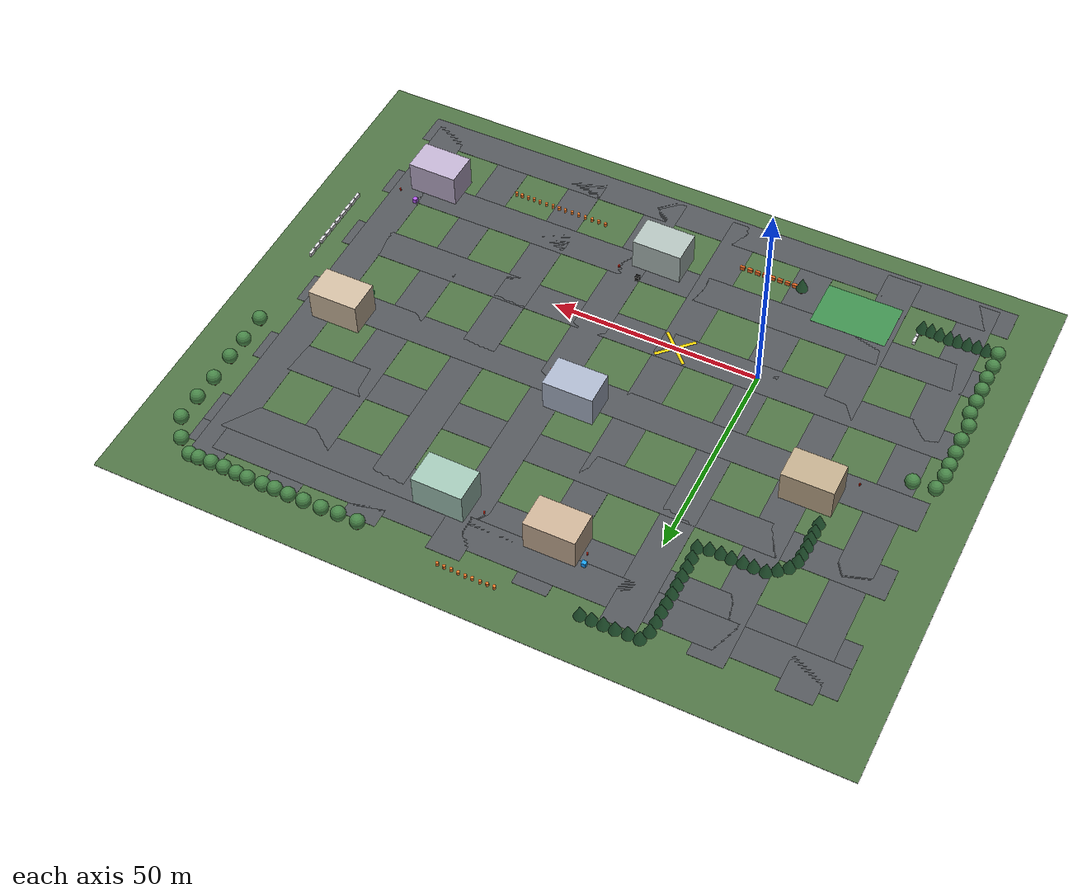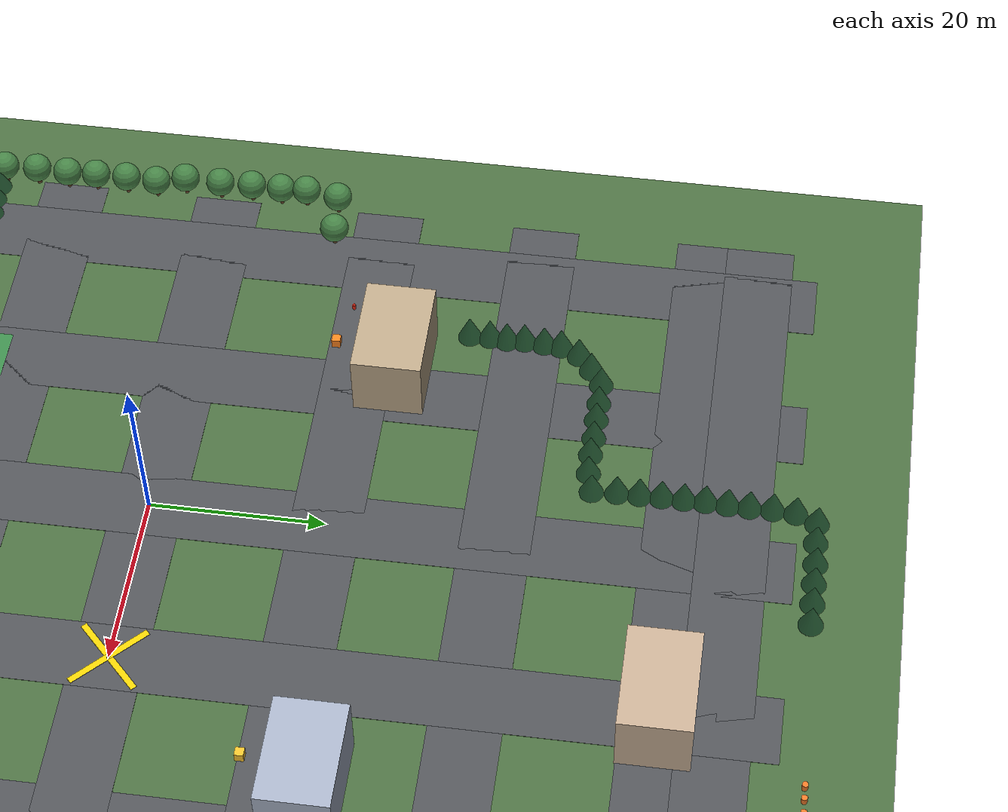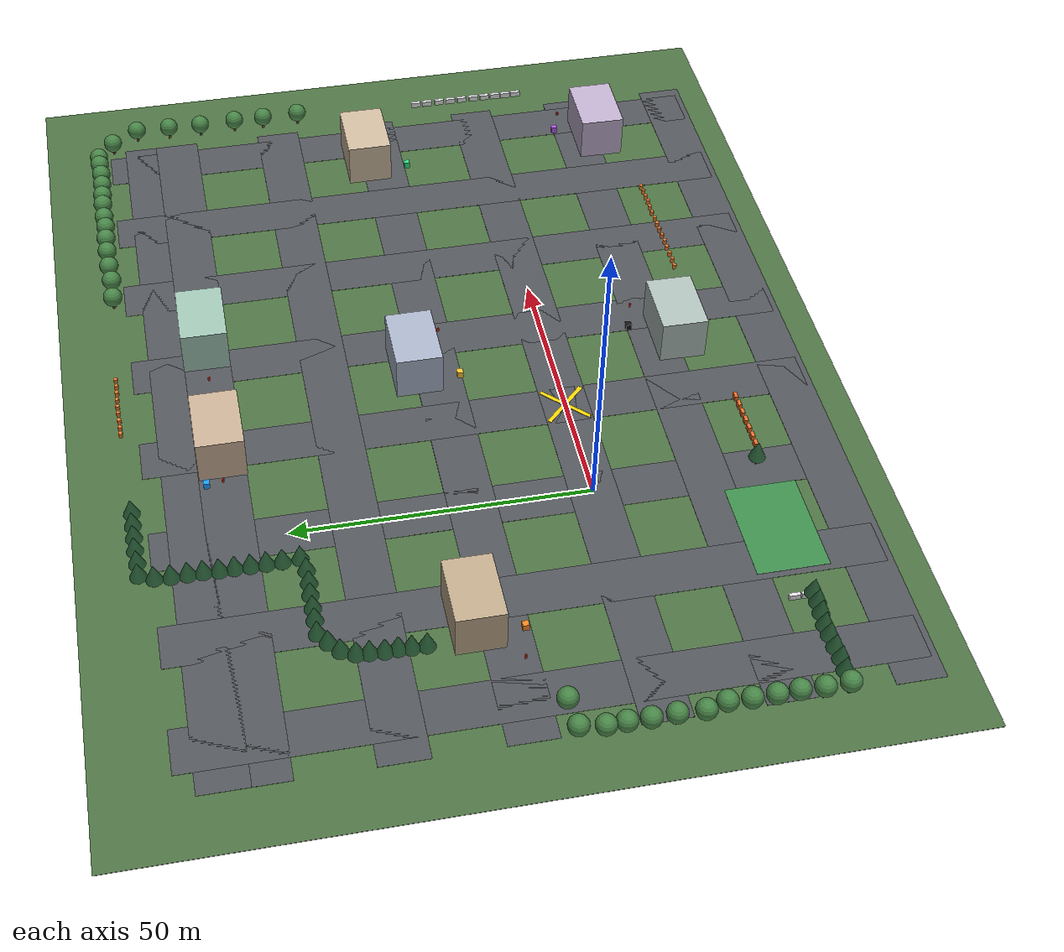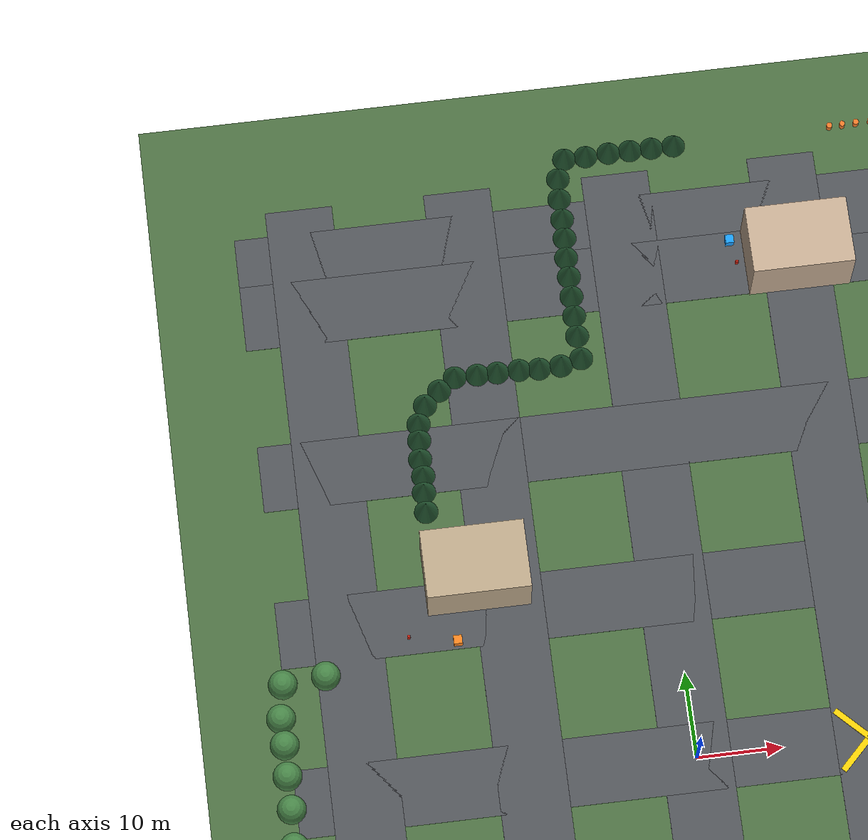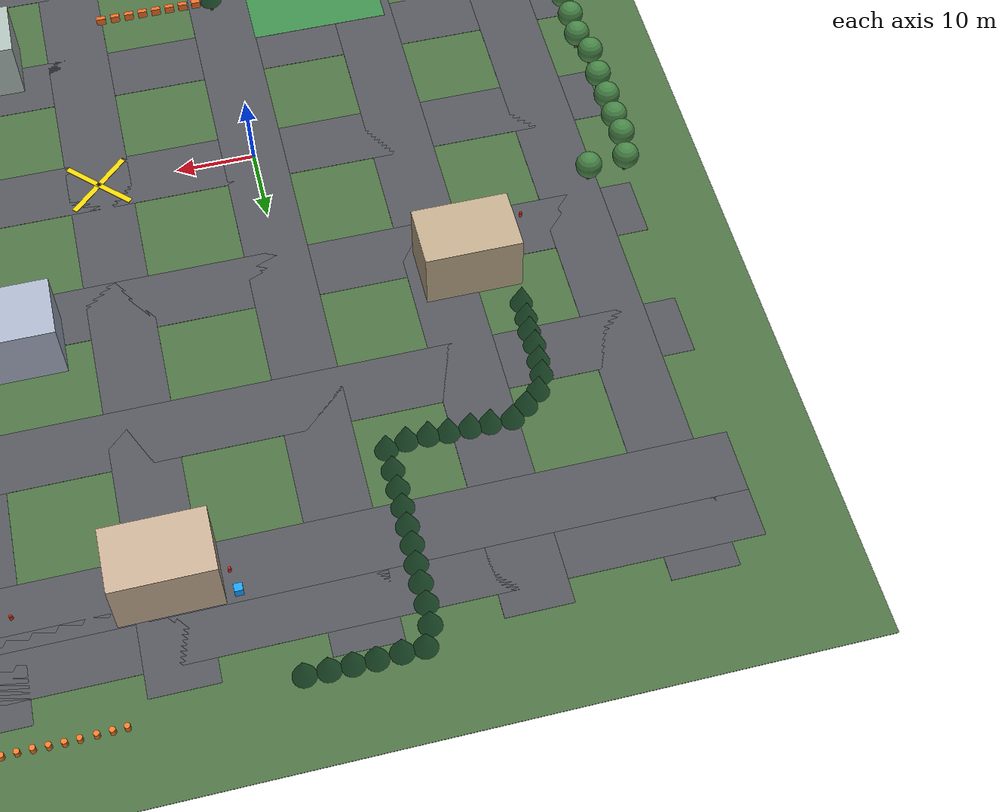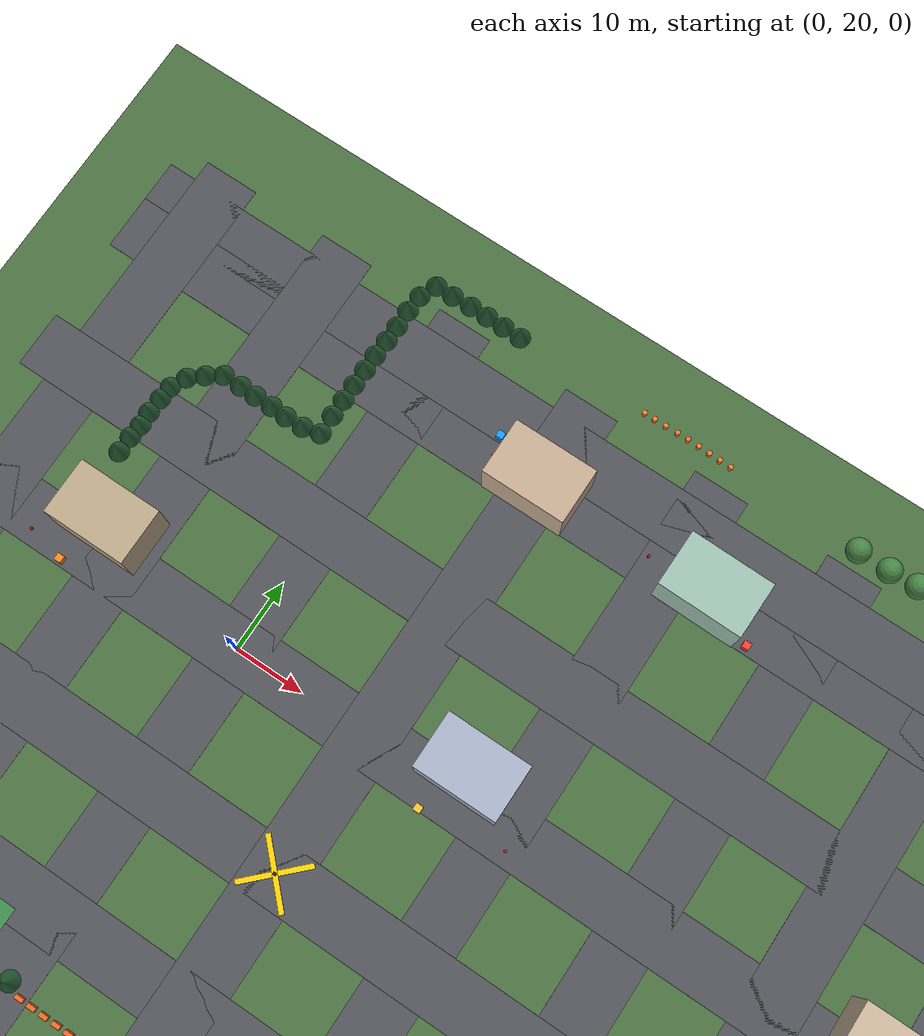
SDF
<?xml version="1.0" ?>
<sdf version="1.9">
  <world name="campus_pucrs">
    <gravity>0 0 -9.8</gravity>
    <physics name="default" type="dartsim">
      <max_step_size>0.01</max_step_size>
      <real_time_factor>1.0</real_time_factor>
    </physics>

    <plugin filename="gz-sim-physics-system" name="gz::sim::systems::Physics"/>
    <plugin filename="gz-sim-user-commands-system" name="gz::sim::systems::UserCommands"/>
    <plugin filename="gz-sim-scene-broadcaster-system" name="gz::sim::systems::SceneBroadcaster"/>
    <plugin filename="gz-sim-sensors-system" name="gz::sim::systems::Sensors">
      <render_engine>ogre2</render_engine>
    </plugin>

    <scene>
      <ambient>0.42 0.46 0.50 1</ambient>
      <background>0.05 0.08 0.12 1</background>
      <shadows>true</shadows>
    </scene>

    <light name="sun" type="directional">
      <pose>30 20 80 0 0 0</pose>
      <cast_shadows>true</cast_shadows>
      <diffuse>0.9 0.92 0.95 1</diffuse>
      <specular>0.25 0.25 0.25 1</specular>
      <direction>-0.35 0.20 -0.90</direction>
    </light>
<model name='campus_ground'>
  <static>true</static>
  <link name='link'>
    <collision name='ground_collision'><pose>31.0 18.0 -0.05 0 0 0.0</pose><geometry><box><size>174.0 132.0 0.1</size></box></geometry><surface><friction><ode><mu>1.0</mu><mu2>1.0</mu2></ode></friction></surface></collision>
    <visual name='ground_visual'><pose>31.0 18.0 -0.05 0 0 0.0</pose><geometry><box><size>174.0 132.0 0.1</size></box></geometry><material><ambient>0.180 0.264 0.156 1</ambient><diffuse>0.3 0.44 0.26 1</diffuse></material></visual>
  </link>
</model>
<model name='robot_spawn_marker_x'>
  <static>true</static>
  <link name='link'>
    <visual name='spawn_marker_arm_a_visual'><pose>20.0 0.0 0.090 0 0 0.785398</pose><geometry><box><size>10.0 0.72 0.08</size></box></geometry><material><ambient>1.0 0.82 0.02 1</ambient><diffuse>1.0 0.82 0.02 1</diffuse><emissive>1.0 0.82 0.02 1</emissive></material></visual>
    <visual name='spawn_marker_arm_b_visual'><pose>20.0 0.0 0.093 0 0 -0.785398</pose><geometry><box><size>10.0 0.72 0.08</size></box></geometry><material><ambient>1.0 0.82 0.02 1</ambient><diffuse>1.0 0.82 0.02 1</diffuse><emissive>1.0 0.82 0.02 1</emissive></material></visual>
  </link>
</model>
<model name='road_v_-38.0'>
  <static>true</static>
  <link name='link'>
    <visual name='road_visual'><pose>-38.0 15.0 0.02 0 0 0.0</pose><geometry><box><size>8.0 114.0 0.04</size></box></geometry><material><ambient>0.192 0.198 0.210 1</ambient><diffuse>0.32 0.33 0.35 1</diffuse></material></visual>
  </link>
</model>
<model name='road_v_-19.0'>
  <static>true</static>
  <link name='link'>
    <visual name='road_visual'><pose>-19.0 15.0 0.02 0 0 0.0</pose><geometry><box><size>8.0 114.0 0.04</size></box></geometry><material><ambient>0.192 0.198 0.210 1</ambient><diffuse>0.32 0.33 0.35 1</diffuse></material></visual>
  </link>
</model>
<model name='road_v_0.0'>
  <static>true</static>
  <link name='link'>
    <visual name='road_visual'><pose>0.0 15.0 0.02 0 0 0.0</pose><geometry><box><size>8.0 114.0 0.04</size></box></geometry><material><ambient>0.192 0.198 0.210 1</ambient><diffuse>0.32 0.33 0.35 1</diffuse></material></visual>
  </link>
</model>
<model name='road_v_20.0'>
  <static>true</static>
  <link name='link'>
    <visual name='road_visual'><pose>20.0 15.0 0.02 0 0 0.0</pose><geometry><box><size>8.0 114.0 0.04</size></box></geometry><material><ambient>0.192 0.198 0.210 1</ambient><diffuse>0.32 0.33 0.35 1</diffuse></material></visual>
  </link>
</model>
<model name='road_v_40.0'>
  <static>true</static>
  <link name='link'>
    <visual name='road_visual'><pose>40.0 15.0 0.02 0 0 0.0</pose><geometry><box><size>8.0 114.0 0.04</size></box></geometry><material><ambient>0.192 0.198 0.210 1</ambient><diffuse>0.32 0.33 0.35 1</diffuse></material></visual>
  </link>
</model>
<model name='road_v_60.0'>
  <static>true</static>
  <link name='link'>
    <visual name='road_visual'><pose>60.0 15.0 0.02 0 0 0.0</pose><geometry><box><size>8.0 114.0 0.04</size></box></geometry><material><ambient>0.192 0.198 0.210 1</ambient><diffuse>0.32 0.33 0.35 1</diffuse></material></visual>
  </link>
</model>
<model name='road_v_79.0'>
  <static>true</static>
  <link name='link'>
    <visual name='road_visual'><pose>79.0 15.0 0.02 0 0 0.0</pose><geometry><box><size>8.0 114.0 0.04</size></box></geometry><material><ambient>0.192 0.198 0.210 1</ambient><diffuse>0.32 0.33 0.35 1</diffuse></material></visual>
  </link>
</model>
<model name='road_v_98.0'>
  <static>true</static>
  <link name='link'>
    <visual name='road_visual'><pose>98.0 15.0 0.02 0 0 0.0</pose><geometry><box><size>8.0 114.0 0.04</size></box></geometry><material><ambient>0.192 0.198 0.210 1</ambient><diffuse>0.32 0.33 0.35 1</diffuse></material></visual>
  </link>
</model>
<model name='road_h_-39.0'>
  <static>true</static>
  <link name='link'>
    <visual name='road_visual'><pose>29.0 -39.0 0.02 0 0 0.0</pose><geometry><box><size>150.0 8.0 0.04</size></box></geometry><material><ambient>0.192 0.198 0.210 1</ambient><diffuse>0.32 0.33 0.35 1</diffuse></material></visual>
  </link>
</model>
<model name='road_h_-19.0'>
  <static>true</static>
  <link name='link'>
    <visual name='road_visual'><pose>29.0 -19.0 0.02 0 0 0.0</pose><geometry><box><size>150.0 8.0 0.04</size></box></geometry><material><ambient>0.192 0.198 0.210 1</ambient><diffuse>0.32 0.33 0.35 1</diffuse></material></visual>
  </link>
</model>
<model name='road_h_0.0'>
  <static>true</static>
  <link name='link'>
    <visual name='road_visual'><pose>29.0 0.0 0.02 0 0 0.0</pose><geometry><box><size>150.0 8.0 0.04</size></box></geometry><material><ambient>0.192 0.198 0.210 1</ambient><diffuse>0.32 0.33 0.35 1</diffuse></material></visual>
  </link>
</model>
<model name='road_h_20.0'>
  <static>true</static>
  <link name='link'>
    <visual name='road_visual'><pose>29.0 20.0 0.02 0 0 0.0</pose><geometry><box><size>150.0 8.0 0.04</size></box></geometry><material><ambient>0.192 0.198 0.210 1</ambient><diffuse>0.32 0.33 0.35 1</diffuse></material></visual>
  </link>
</model>
<model name='road_h_39.0'>
  <static>true</static>
  <link name='link'>
    <visual name='road_visual'><pose>29.0 39.0 0.02 0 0 0.0</pose><geometry><box><size>150.0 8.0 0.04</size></box></geometry><material><ambient>0.192 0.198 0.210 1</ambient><diffuse>0.32 0.33 0.35 1</diffuse></material></visual>
  </link>
</model>
<model name='road_h_59.0'>
  <static>true</static>
  <link name='link'>
    <visual name='road_visual'><pose>29.0 59.0 0.02 0 0 0.0</pose><geometry><box><size>150.0 8.0 0.04</size></box></geometry><material><ambient>0.192 0.198 0.210 1</ambient><diffuse>0.32 0.33 0.35 1</diffuse></material></visual>
  </link>
</model>
<model name='road_h_65.0'>
  <static>true</static>
  <link name='link'>
    <visual name='road_visual'><pose>29.0 65.0 0.02 0 0 0.0</pose><geometry><box><size>150.0 8.0 0.04</size></box></geometry><material><ambient>0.192 0.198 0.210 1</ambient><diffuse>0.32 0.33 0.35 1</diffuse></material></visual>
  </link>
</model>
<model name='school_1'>
  <static>true</static>
  <link name='link'>
    <collision name='body_collision'><pose>-22.51 24.33 4.0 0 0 0.0</pose><geometry><box><size>12 8 8</size></box></geometry></collision>
    <visual name='body_visual'><pose>-22.51 24.33 4.0 0 0 0.0</pose><geometry><box><size>12 8 8</size></box></geometry><material><ambient>0.444 0.396 0.324 1</ambient><diffuse>0.74 0.66 0.54 1</diffuse></material></visual>
  </link>
</model>
<model name='school_2'>
  <static>true</static>
  <link name='link'>
    <collision name='body_collision'><pose>33.17 23.81 4.0 0 0 0.0</pose><geometry><box><size>12 8 8</size></box></geometry></collision>
    <visual name='body_visual'><pose>33.17 23.81 4.0 0 0 0.0</pose><geometry><box><size>12 8 8</size></box></geometry><material><ambient>0.396 0.420 0.468 1</ambient><diffuse>0.66 0.7 0.78 1</diffuse></material></visual>
  </link>
</model>
<model name='school_3'>
  <static>true</static>
  <link name='link'>
    <collision name='body_collision'><pose>92.17 23.02 4.0 0 0 0.0</pose><geometry><box><size>12 8 8</size></box></geometry></collision>
    <visual name='body_visual'><pose>92.17 23.02 4.0 0 0 0.0</pose><geometry><box><size>12 8 8</size></box></geometry><material><ambient>0.480 0.432 0.372 1</ambient><diffuse>0.8 0.72 0.62 1</diffuse></material></visual>
  </link>
</model>
<model name='school_4'>
  <static>true</static>
  <link name='link'>
    <collision name='body_collision'><pose>45.89 58.97 4.0 0 0 1.56</pose><geometry><box><size>8 12 8</size></box></geometry></collision>
    <visual name='body_visual'><pose>45.89 58.97 4.0 0 0 1.56</pose><geometry><box><size>8 12 8</size></box></geometry><material><ambient>0.372 0.456 0.420 1</ambient><diffuse>0.62 0.76 0.7 1</diffuse></material></visual>
  </link>
</model>
<model name='school_5'>
  <static>true</static>
  <link name='link'>
    <collision name='body_collision'><pose>91.89 -22.61 4.0 0 0 3.13</pose><geometry><box><size>12 8 8</size></box></geometry></collision>
    <visual name='body_visual'><pose>91.89 -22.61 4.0 0 0 3.13</pose><geometry><box><size>12 8 8</size></box></geometry><material><ambient>0.444 0.408 0.480 1</ambient><diffuse>0.74 0.68 0.8 1</diffuse></material></visual>
  </link>
</model>
<model name='school_6'>
  <static>true</static>
  <link name='link'>
    <collision name='body_collision'><pose>33.47 -22.74 4.0 0 0 3.13</pose><geometry><box><size>12 8 8</size></box></geometry></collision>
    <visual name='body_visual'><pose>33.47 -22.74 4.0 0 0 3.13</pose><geometry><box><size>12 8 8</size></box></geometry><material><ambient>0.408 0.444 0.432 1</ambient><diffuse>0.68 0.74 0.72 1</diffuse></material></visual>
  </link>
</model>
<model name='school_7'>
  <static>true</static>
  <link name='link'>
    <collision name='body_collision'><pose>19.96 58.89 4.0 0 0 -1.57</pose><geometry><box><size>8 12 8</size></box></geometry></collision>
    <visual name='body_visual'><pose>19.96 58.89 4.0 0 0 -1.57</pose><geometry><box><size>8 12 8</size></box></geometry><material><ambient>0.468 0.408 0.348 1</ambient><diffuse>0.78 0.68 0.58 1</diffuse></material></visual>
  </link>
</model>
<model name='robocup_field'>
  <static>true</static>
  <link name='link'>
    <visual name='field_visual'><pose>-12.92 -26.97 0.03 0 0 0.0</pose><geometry><box><size>18.0 12.0 0.06</size></box></geometry><material><ambient>0.144 0.330 0.180 1</ambient><diffuse>0.24 0.55 0.3 1</diffuse></material></visual>
  </link>
</model>
<model name='oak_tree_0'>
  <static>true</static>
  <link name='link'>
    <collision name='trunk_collision'><pose>-45.8507 -27.6084 0.8 0.0 0.0 0</pose><geometry><cylinder><radius>0.25</radius><length>1.6</length></cylinder></geometry></collision>
    <visual name='trunk_visual'><pose>-45.8507 -27.6084 0.8 0.0 0.0 0</pose><geometry><cylinder><radius>0.25</radius><length>1.6</length></cylinder></geometry><material><ambient>0.252 0.180 0.108 1</ambient><diffuse>0.42 0.3 0.18 1</diffuse></material></visual>
    <visual name='crown_visual'><pose>-45.8507 -27.6084 2.6 0 0 0</pose><geometry><sphere><radius>1.7</radius></sphere></geometry><material><ambient>0.168 0.312 0.168 1</ambient><diffuse>0.28 0.52 0.28 1</diffuse></material></visual>
  </link>
</model>
<model name='oak_tree_1'>
  <static>true</static>
  <link name='link'>
    <collision name='trunk_collision'><pose>58.7873 73.9068 0.8 0.0 0.0 0</pose><geometry><cylinder><radius>0.25</radius><length>1.6</length></cylinder></geometry></collision>
    <visual name='trunk_visual'><pose>58.7873 73.9068 0.8 0.0 0.0 0</pose><geometry><cylinder><radius>0.25</radius><length>1.6</length></cylinder></geometry><material><ambient>0.252 0.180 0.108 1</ambient><diffuse>0.42 0.3 0.18 1</diffuse></material></visual>
    <visual name='crown_visual'><pose>58.7873 73.9068 2.6 0 0 0</pose><geometry><sphere><radius>1.7</radius></sphere></geometry><material><ambient>0.168 0.312 0.168 1</ambient><diffuse>0.28 0.52 0.28 1</diffuse></material></visual>
  </link>
</model>
<model name='oak_tree_2'>
  <static>true</static>
  <link name='link'>
    <collision name='trunk_collision'><pose>63.3588 73.8542 0.8 0.0 0.0 0</pose><geometry><cylinder><radius>0.25</radius><length>1.6</length></cylinder></geometry></collision>
    <visual name='trunk_visual'><pose>63.3588 73.8542 0.8 0.0 0.0 0</pose><geometry><cylinder><radius>0.25</radius><length>1.6</length></cylinder></geometry><material><ambient>0.252 0.180 0.108 1</ambient><diffuse>0.42 0.3 0.18 1</diffuse></material></visual>
    <visual name='crown_visual'><pose>63.3588 73.8542 2.6 0 0 0</pose><geometry><sphere><radius>1.7</radius></sphere></geometry><material><ambient>0.168 0.312 0.168 1</ambient><diffuse>0.28 0.52 0.28 1</diffuse></material></visual>
  </link>
</model>
<model name='oak_tree_3'>
  <static>true</static>
  <link name='link'>
    <collision name='trunk_collision'><pose>67.3848 74.0914 0.8 0.0 0.0 0</pose><geometry><cylinder><radius>0.25</radius><length>1.6</length></cylinder></geometry></collision>
    <visual name='trunk_visual'><pose>67.3848 74.0914 0.8 0.0 0.0 0</pose><geometry><cylinder><radius>0.25</radius><length>1.6</length></cylinder></geometry><material><ambient>0.252 0.180 0.108 1</ambient><diffuse>0.42 0.3 0.18 1</diffuse></material></visual>
    <visual name='crown_visual'><pose>67.3848 74.0914 2.6 0 0 0</pose><geometry><sphere><radius>1.7</radius></sphere></geometry><material><ambient>0.168 0.312 0.168 1</ambient><diffuse>0.28 0.52 0.28 1</diffuse></material></visual>
  </link>
</model>
<model name='oak_tree_4'>
  <static>true</static>
  <link name='link'>
    <collision name='trunk_collision'><pose>71.6046 74.1445 0.8 0.0 0.0 0</pose><geometry><cylinder><radius>0.25</radius><length>1.6</length></cylinder></geometry></collision>
    <visual name='trunk_visual'><pose>71.6046 74.1445 0.8 0.0 0.0 0</pose><geometry><cylinder><radius>0.25</radius><length>1.6</length></cylinder></geometry><material><ambient>0.252 0.180 0.108 1</ambient><diffuse>0.42 0.3 0.18 1</diffuse></material></visual>
    <visual name='crown_visual'><pose>71.6046 74.1445 2.6 0 0 0</pose><geometry><sphere><radius>1.7</radius></sphere></geometry><material><ambient>0.168 0.312 0.168 1</ambient><diffuse>0.28 0.52 0.28 1</diffuse></material></visual>
  </link>
</model>
<model name='oak_tree_5'>
  <static>true</static>
  <link name='link'>
    <collision name='trunk_collision'><pose>99.8071 74.0512 0.8 0.0 0.0 0</pose><geometry><cylinder><radius>0.25</radius><length>1.6</length></cylinder></geometry></collision>
    <visual name='trunk_visual'><pose>99.8071 74.0512 0.8 0.0 0.0 0</pose><geometry><cylinder><radius>0.25</radius><length>1.6</length></cylinder></geometry><material><ambient>0.252 0.180 0.108 1</ambient><diffuse>0.42 0.3 0.18 1</diffuse></material></visual>
    <visual name='crown_visual'><pose>99.8071 74.0512 2.6 0 0 0</pose><geometry><sphere><radius>1.7</radius></sphere></geometry><material><ambient>0.168 0.312 0.168 1</ambient><diffuse>0.28 0.52 0.28 1</diffuse></material></visual>
  </link>
</model>
<model name='oak_tree_6'>
  <static>true</static>
  <link name='link'>
    <collision name='trunk_collision'><pose>103.833 71.1472 0.8 0.0 0.0 0</pose><geometry><cylinder><radius>0.25</radius><length>1.6</length></cylinder></geometry></collision>
    <visual name='trunk_visual'><pose>103.833 71.1472 0.8 0.0 0.0 0</pose><geometry><cylinder><radius>0.25</radius><length>1.6</length></cylinder></geometry><material><ambient>0.252 0.180 0.108 1</ambient><diffuse>0.42 0.3 0.18 1</diffuse></material></visual>
    <visual name='crown_visual'><pose>103.833 71.1472 2.6 0 0 0</pose><geometry><sphere><radius>1.7</radius></sphere></geometry><material><ambient>0.168 0.312 0.168 1</ambient><diffuse>0.28 0.52 0.28 1</diffuse></material></visual>
  </link>
</model>
<model name='oak_tree_7'>
  <static>true</static>
  <link name='link'>
    <collision name='trunk_collision'><pose>107.085 66.2785 0.8 0.0 0.0 0</pose><geometry><cylinder><radius>0.25</radius><length>1.6</length></cylinder></geometry></collision>
    <visual name='trunk_visual'><pose>107.085 66.2785 0.8 0.0 0.0 0</pose><geometry><cylinder><radius>0.25</radius><length>1.6</length></cylinder></geometry><material><ambient>0.252 0.180 0.108 1</ambient><diffuse>0.42 0.3 0.18 1</diffuse></material></visual>
    <visual name='crown_visual'><pose>107.085 66.2785 2.6 0 0 0</pose><geometry><sphere><radius>1.7</radius></sphere></geometry><material><ambient>0.168 0.312 0.168 1</ambient><diffuse>0.28 0.52 0.28 1</diffuse></material></visual>
  </link>
</model>
<model name='oak_tree_8'>
  <static>true</static>
  <link name='link'>
    <collision name='trunk_collision'><pose>107.0 60.0 0.8 0.0 0.0 0</pose><geometry><cylinder><radius>0.25</radius><length>1.6</length></cylinder></geometry></collision>
    <visual name='trunk_visual'><pose>107.0 60.0 0.8 0.0 0.0 0</pose><geometry><cylinder><radius>0.25</radius><length>1.6</length></cylinder></geometry><material><ambient>0.252 0.180 0.108 1</ambient><diffuse>0.42 0.3 0.18 1</diffuse></material></visual>
    <visual name='crown_visual'><pose>107.0 60.0 2.6 0 0 0</pose><geometry><sphere><radius>1.7</radius></sphere></geometry><material><ambient>0.168 0.312 0.168 1</ambient><diffuse>0.28 0.52 0.28 1</diffuse></material></visual>
  </link>
</model>
<model name='oak_tree_9'>
  <static>true</static>
  <link name='link'>
    <collision name='trunk_collision'><pose>106.778 53.8309 0.8 0.0 0.0 0</pose><geometry><cylinder><radius>0.25</radius><length>1.6</length></cylinder></geometry></collision>
    <visual name='trunk_visual'><pose>106.778 53.8309 0.8 0.0 0.0 0</pose><geometry><cylinder><radius>0.25</radius><length>1.6</length></cylinder></geometry><material><ambient>0.252 0.180 0.108 1</ambient><diffuse>0.42 0.3 0.18 1</diffuse></material></visual>
    <visual name='crown_visual'><pose>106.778 53.8309 2.6 0 0 0</pose><geometry><sphere><radius>1.7</radius></sphere></geometry><material><ambient>0.168 0.312 0.168 1</ambient><diffuse>0.28 0.52 0.28 1</diffuse></material></visual>
  </link>
</model>
<model name='oak_tree_10'>
  <static>true</static>
  <link name='link'>
    <collision name='trunk_collision'><pose>106.957 47.0737 0.8 0.0 0.0 0</pose><geometry><cylinder><radius>0.25</radius><length>1.6</length></cylinder></geometry></collision>
    <visual name='trunk_visual'><pose>106.957 47.0737 0.8 0.0 0.0 0</pose><geometry><cylinder><radius>0.25</radius><length>1.6</length></cylinder></geometry><material><ambient>0.252 0.180 0.108 1</ambient><diffuse>0.42 0.3 0.18 1</diffuse></material></visual>
    <visual name='crown_visual'><pose>106.957 47.0737 2.6 0 0 0</pose><geometry><sphere><radius>1.7</radius></sphere></geometry><material><ambient>0.168 0.312 0.168 1</ambient><diffuse>0.28 0.52 0.28 1</diffuse></material></visual>
  </link>
</model>
<model name='oak_tree_11'>
  <static>true</static>
  <link name='link'>
    <collision name='trunk_collision'><pose>106.932 41.4 0.8 0.0 0.0 0</pose><geometry><cylinder><radius>0.25</radius><length>1.6</length></cylinder></geometry></collision>
    <visual name='trunk_visual'><pose>106.932 41.4 0.8 0.0 0.0 0</pose><geometry><cylinder><radius>0.25</radius><length>1.6</length></cylinder></geometry><material><ambient>0.252 0.180 0.108 1</ambient><diffuse>0.42 0.3 0.18 1</diffuse></material></visual>
    <visual name='crown_visual'><pose>106.932 41.4 2.6 0 0 0</pose><geometry><sphere><radius>1.7</radius></sphere></geometry><material><ambient>0.168 0.312 0.168 1</ambient><diffuse>0.28 0.52 0.28 1</diffuse></material></visual>
  </link>
</model>
<model name='oak_tree_12'>
  <static>true</static>
  <link name='link'>
    <collision name='trunk_collision'><pose>107.049 34.5471 0.8 0.0 0.0 0</pose><geometry><cylinder><radius>0.25</radius><length>1.6</length></cylinder></geometry></collision>
    <visual name='trunk_visual'><pose>107.049 34.5471 0.8 0.0 0.0 0</pose><geometry><cylinder><radius>0.25</radius><length>1.6</length></cylinder></geometry><material><ambient>0.252 0.180 0.108 1</ambient><diffuse>0.42 0.3 0.18 1</diffuse></material></visual>
    <visual name='crown_visual'><pose>107.049 34.5471 2.6 0 0 0</pose><geometry><sphere><radius>1.7</radius></sphere></geometry><material><ambient>0.168 0.312 0.168 1</ambient><diffuse>0.28 0.52 0.28 1</diffuse></material></visual>
  </link>
</model>
<model name='oak_tree_13'>
  <static>true</static>
  <link name='link'>
    <collision name='trunk_collision'><pose>75.2969 74.1503 0.8 0.0 0.0 0</pose><geometry><cylinder><radius>0.25</radius><length>1.6</length></cylinder></geometry></collision>
    <visual name='trunk_visual'><pose>75.2969 74.1503 0.8 0.0 0.0 0</pose><geometry><cylinder><radius>0.25</radius><length>1.6</length></cylinder></geometry><material><ambient>0.252 0.180 0.108 1</ambient><diffuse>0.42 0.3 0.18 1</diffuse></material></visual>
    <visual name='crown_visual'><pose>75.2969 74.1503 2.6 0 0 0</pose><geometry><sphere><radius>1.7</radius></sphere></geometry><material><ambient>0.168 0.312 0.168 1</ambient><diffuse>0.28 0.52 0.28 1</diffuse></material></visual>
  </link>
</model>
<model name='oak_tree_14'>
  <static>true</static>
  <link name='link'>
    <collision name='trunk_collision'><pose>78.6553 74.017 0.8 0.0 0.0 0</pose><geometry><cylinder><radius>0.25</radius><length>1.6</length></cylinder></geometry></collision>
    <visual name='trunk_visual'><pose>78.6553 74.017 0.8 0.0 0.0 0</pose><geometry><cylinder><radius>0.25</radius><length>1.6</length></cylinder></geometry><material><ambient>0.252 0.180 0.108 1</ambient><diffuse>0.42 0.3 0.18 1</diffuse></material></visual>
    <visual name='crown_visual'><pose>78.6553 74.017 2.6 0 0 0</pose><geometry><sphere><radius>1.7</radius></sphere></geometry><material><ambient>0.168 0.312 0.168 1</ambient><diffuse>0.28 0.52 0.28 1</diffuse></material></visual>
  </link>
</model>
<model name='oak_tree_15'>
  <static>true</static>
  <link name='link'>
    <collision name='trunk_collision'><pose>81.5914 74.1371 0.8 0.0 0.0 0</pose><geometry><cylinder><radius>0.25</radius><length>1.6</length></cylinder></geometry></collision>
    <visual name='trunk_visual'><pose>81.5914 74.1371 0.8 0.0 0.0 0</pose><geometry><cylinder><radius>0.25</radius><length>1.6</length></cylinder></geometry><material><ambient>0.252 0.180 0.108 1</ambient><diffuse>0.42 0.3 0.18 1</diffuse></material></visual>
    <visual name='crown_visual'><pose>81.5914 74.1371 2.6 0 0 0</pose><geometry><sphere><radius>1.7</radius></sphere></geometry><material><ambient>0.168 0.312 0.168 1</ambient><diffuse>0.28 0.52 0.28 1</diffuse></material></visual>
  </link>
</model>
<model name='oak_tree_16'>
  <static>true</static>
  <link name='link'>
    <collision name='trunk_collision'><pose>85.3365 74.1434 0.8 0.0 0.0 0</pose><geometry><cylinder><radius>0.25</radius><length>1.6</length></cylinder></geometry></collision>
    <visual name='trunk_visual'><pose>85.3365 74.1434 0.8 0.0 0.0 0</pose><geometry><cylinder><radius>0.25</radius><length>1.6</length></cylinder></geometry><material><ambient>0.252 0.180 0.108 1</ambient><diffuse>0.42 0.3 0.18 1</diffuse></material></visual>
    <visual name='crown_visual'><pose>85.3365 74.1434 2.6 0 0 0</pose><geometry><sphere><radius>1.7</radius></sphere></geometry><material><ambient>0.168 0.312 0.168 1</ambient><diffuse>0.28 0.52 0.28 1</diffuse></material></visual>
  </link>
</model>
<model name='oak_tree_17'>
  <static>true</static>
  <link name='link'>
    <collision name='trunk_collision'><pose>88.1147 74.0554 0.8 0.0 0.0 0</pose><geometry><cylinder><radius>0.25</radius><length>1.6</length></cylinder></geometry></collision>
    <visual name='trunk_visual'><pose>88.1147 74.0554 0.8 0.0 0.0 0</pose><geometry><cylinder><radius>0.25</radius><length>1.6</length></cylinder></geometry><material><ambient>0.252 0.180 0.108 1</ambient><diffuse>0.42 0.3 0.18 1</diffuse></material></visual>
    <visual name='crown_visual'><pose>88.1147 74.0554 2.6 0 0 0</pose><geometry><sphere><radius>1.7</radius></sphere></geometry><material><ambient>0.168 0.312 0.168 1</ambient><diffuse>0.28 0.52 0.28 1</diffuse></material></visual>
  </link>
</model>
<model name='oak_tree_18'>
  <static>true</static>
  <link name='link'>
    <collision name='trunk_collision'><pose>91.2972 73.9451 0.8 0.0 0.0 0</pose><geometry><cylinder><radius>0.25</radius><length>1.6</length></cylinder></geometry></collision>
    <visual name='trunk_visual'><pose>91.2972 73.9451 0.8 0.0 0.0 0</pose><geometry><cylinder><radius>0.25</radius><length>1.6</length></cylinder></geometry><material><ambient>0.252 0.180 0.108 1</ambient><diffuse>0.42 0.3 0.18 1</diffuse></material></visual>
    <visual name='crown_visual'><pose>91.2972 73.9451 2.6 0 0 0</pose><geometry><sphere><radius>1.7</radius></sphere></geometry><material><ambient>0.168 0.312 0.168 1</ambient><diffuse>0.28 0.52 0.28 1</diffuse></material></visual>
  </link>
</model>
<model name='oak_tree_19'>
  <static>true</static>
  <link name='link'>
    <collision name='trunk_collision'><pose>94.4973 73.927 0.8 0.0 0.0 0</pose><geometry><cylinder><radius>0.25</radius><length>1.6</length></cylinder></geometry></collision>
    <visual name='trunk_visual'><pose>94.4973 73.927 0.8 0.0 0.0 0</pose><geometry><cylinder><radius>0.25</radius><length>1.6</length></cylinder></geometry><material><ambient>0.252 0.180 0.108 1</ambient><diffuse>0.42 0.3 0.18 1</diffuse></material></visual>
    <visual name='crown_visual'><pose>94.4973 73.927 2.6 0 0 0</pose><geometry><sphere><radius>1.7</radius></sphere></geometry><material><ambient>0.168 0.312 0.168 1</ambient><diffuse>0.28 0.52 0.28 1</diffuse></material></visual>
  </link>
</model>
<model name='oak_tree_20'>
  <static>true</static>
  <link name='link'>
    <collision name='trunk_collision'><pose>97.5564 74.0473 0.8 0.0 0.0 0</pose><geometry><cylinder><radius>0.25</radius><length>1.6</length></cylinder></geometry></collision>
    <visual name='trunk_visual'><pose>97.5564 74.0473 0.8 0.0 0.0 0</pose><geometry><cylinder><radius>0.25</radius><length>1.6</length></cylinder></geometry><material><ambient>0.252 0.180 0.108 1</ambient><diffuse>0.42 0.3 0.18 1</diffuse></material></visual>
    <visual name='crown_visual'><pose>97.5564 74.0473 2.6 0 0 0</pose><geometry><sphere><radius>1.7</radius></sphere></geometry><material><ambient>0.168 0.312 0.168 1</ambient><diffuse>0.28 0.52 0.28 1</diffuse></material></visual>
  </link>
</model>
<model name='oak_tree_21'>
  <static>true</static>
  <link name='link'>
    <collision name='trunk_collision'><pose>-46.0054 -23.6481 0.8 0.0 0.0 0</pose><geometry><cylinder><radius>0.25</radius><length>1.6</length></cylinder></geometry></collision>
    <visual name='trunk_visual'><pose>-46.0054 -23.6481 0.8 0.0 0.0 0</pose><geometry><cylinder><radius>0.25</radius><length>1.6</length></cylinder></geometry><material><ambient>0.252 0.180 0.108 1</ambient><diffuse>0.42 0.3 0.18 1</diffuse></material></visual>
    <visual name='crown_visual'><pose>-46.0054 -23.6481 2.6 0 0 0</pose><geometry><sphere><radius>1.7</radius></sphere></geometry><material><ambient>0.168 0.312 0.168 1</ambient><diffuse>0.28 0.52 0.28 1</diffuse></material></visual>
  </link>
</model>
<model name='oak_tree_22'>
  <static>true</static>
  <link name='link'>
    <collision name='trunk_collision'><pose>-45.853 -19.83 0.8 0.0 0.0 0</pose><geometry><cylinder><radius>0.25</radius><length>1.6</length></cylinder></geometry></collision>
    <visual name='trunk_visual'><pose>-45.853 -19.83 0.8 0.0 0.0 0</pose><geometry><cylinder><radius>0.25</radius><length>1.6</length></cylinder></geometry><material><ambient>0.252 0.180 0.108 1</ambient><diffuse>0.42 0.3 0.18 1</diffuse></material></visual>
    <visual name='crown_visual'><pose>-45.853 -19.83 2.6 0 0 0</pose><geometry><sphere><radius>1.7</radius></sphere></geometry><material><ambient>0.168 0.312 0.168 1</ambient><diffuse>0.28 0.52 0.28 1</diffuse></material></visual>
  </link>
</model>
<model name='oak_tree_23'>
  <static>true</static>
  <link name='link'>
    <collision name='trunk_collision'><pose>-45.9444 -16.2895 0.8 0.0 0.0 0</pose><geometry><cylinder><radius>0.25</radius><length>1.6</length></cylinder></geometry></collision>
    <visual name='trunk_visual'><pose>-45.9444 -16.2895 0.8 0.0 0.0 0</pose><geometry><cylinder><radius>0.25</radius><length>1.6</length></cylinder></geometry><material><ambient>0.252 0.180 0.108 1</ambient><diffuse>0.42 0.3 0.18 1</diffuse></material></visual>
    <visual name='crown_visual'><pose>-45.9444 -16.2895 2.6 0 0 0</pose><geometry><sphere><radius>1.7</radius></sphere></geometry><material><ambient>0.168 0.312 0.168 1</ambient><diffuse>0.28 0.52 0.28 1</diffuse></material></visual>
  </link>
</model>
<model name='oak_tree_24'>
  <static>true</static>
  <link name='link'>
    <collision name='trunk_collision'><pose>-45.9615 -12.5098 0.8 0.0 0.0 0</pose><geometry><cylinder><radius>0.25</radius><length>1.6</length></cylinder></geometry></collision>
    <visual name='trunk_visual'><pose>-45.9615 -12.5098 0.8 0.0 0.0 0</pose><geometry><cylinder><radius>0.25</radius><length>1.6</length></cylinder></geometry><material><ambient>0.252 0.180 0.108 1</ambient><diffuse>0.42 0.3 0.18 1</diffuse></material></visual>
    <visual name='crown_visual'><pose>-45.9615 -12.5098 2.6 0 0 0</pose><geometry><sphere><radius>1.7</radius></sphere></geometry><material><ambient>0.168 0.312 0.168 1</ambient><diffuse>0.28 0.52 0.28 1</diffuse></material></visual>
  </link>
</model>
<model name='oak_tree_25'>
  <static>true</static>
  <link name='link'>
    <collision name='trunk_collision'><pose>-45.8262 -8.78087 0.8 0.0 0.0 0</pose><geometry><cylinder><radius>0.25</radius><length>1.6</length></cylinder></geometry></collision>
    <visual name='trunk_visual'><pose>-45.8262 -8.78087 0.8 0.0 0.0 0</pose><geometry><cylinder><radius>0.25</radius><length>1.6</length></cylinder></geometry><material><ambient>0.252 0.180 0.108 1</ambient><diffuse>0.42 0.3 0.18 1</diffuse></material></visual>
    <visual name='crown_visual'><pose>-45.8262 -8.78087 2.6 0 0 0</pose><geometry><sphere><radius>1.7</radius></sphere></geometry><material><ambient>0.168 0.312 0.168 1</ambient><diffuse>0.28 0.52 0.28 1</diffuse></material></visual>
  </link>
</model>
<model name='oak_tree_26'>
  <static>true</static>
  <link name='link'>
    <collision name='trunk_collision'><pose>-46.7063 -5.35408 0.8 0.0 0.0 0</pose><geometry><cylinder><radius>0.25</radius><length>1.6</length></cylinder></geometry></collision>
    <visual name='trunk_visual'><pose>-46.7063 -5.35408 0.8 0.0 0.0 0</pose><geometry><cylinder><radius>0.25</radius><length>1.6</length></cylinder></geometry><material><ambient>0.252 0.180 0.108 1</ambient><diffuse>0.42 0.3 0.18 1</diffuse></material></visual>
    <visual name='crown_visual'><pose>-46.7063 -5.35408 2.6 0 0 0</pose><geometry><sphere><radius>1.7</radius></sphere></geometry><material><ambient>0.168 0.312 0.168 1</ambient><diffuse>0.28 0.52 0.28 1</diffuse></material></visual>
  </link>
</model>
<model name='oak_tree_27'>
  <static>true</static>
  <link name='link'>
    <collision name='trunk_collision'><pose>-46.5387 -1.00848 0.8 0.0 0.0 0</pose><geometry><cylinder><radius>0.25</radius><length>1.6</length></cylinder></geometry></collision>
    <visual name='trunk_visual'><pose>-46.5387 -1.00848 0.8 0.0 0.0 0</pose><geometry><cylinder><radius>0.25</radius><length>1.6</length></cylinder></geometry><material><ambient>0.252 0.180 0.108 1</ambient><diffuse>0.42 0.3 0.18 1</diffuse></material></visual>
    <visual name='crown_visual'><pose>-46.5387 -1.00848 2.6 0 0 0</pose><geometry><sphere><radius>1.7</radius></sphere></geometry><material><ambient>0.168 0.312 0.168 1</ambient><diffuse>0.28 0.52 0.28 1</diffuse></material></visual>
  </link>
</model>
<model name='oak_tree_28'>
  <static>true</static>
  <link name='link'>
    <collision name='trunk_collision'><pose>-46.5984 2.87375 0.8 0.0 0.0 0</pose><geometry><cylinder><radius>0.25</radius><length>1.6</length></cylinder></geometry></collision>
    <visual name='trunk_visual'><pose>-46.5984 2.87375 0.8 0.0 0.0 0</pose><geometry><cylinder><radius>0.25</radius><length>1.6</length></cylinder></geometry><material><ambient>0.252 0.180 0.108 1</ambient><diffuse>0.42 0.3 0.18 1</diffuse></material></visual>
    <visual name='crown_visual'><pose>-46.5984 2.87375 2.6 0 0 0</pose><geometry><sphere><radius>1.7</radius></sphere></geometry><material><ambient>0.168 0.312 0.168 1</ambient><diffuse>0.28 0.52 0.28 1</diffuse></material></visual>
  </link>
</model>
<model name='oak_tree_29'>
  <static>true</static>
  <link name='link'>
    <collision name='trunk_collision'><pose>-46.5377 6.48958 0.8 0.0 0.0 0</pose><geometry><cylinder><radius>0.25</radius><length>1.6</length></cylinder></geometry></collision>
    <visual name='trunk_visual'><pose>-46.5377 6.48958 0.8 0.0 0.0 0</pose><geometry><cylinder><radius>0.25</radius><length>1.6</length></cylinder></geometry><material><ambient>0.252 0.180 0.108 1</ambient><diffuse>0.42 0.3 0.18 1</diffuse></material></visual>
    <visual name='crown_visual'><pose>-46.5377 6.48958 2.6 0 0 0</pose><geometry><sphere><radius>1.7</radius></sphere></geometry><material><ambient>0.168 0.312 0.168 1</ambient><diffuse>0.28 0.52 0.28 1</diffuse></material></visual>
  </link>
</model>
<model name='oak_tree_30'>
  <static>true</static>
  <link name='link'>
    <collision name='trunk_collision'><pose>-46.6255 9.61611 0.8 0.0 0.0 0</pose><geometry><cylinder><radius>0.25</radius><length>1.6</length></cylinder></geometry></collision>
    <visual name='trunk_visual'><pose>-46.6255 9.61611 0.8 0.0 0.0 0</pose><geometry><cylinder><radius>0.25</radius><length>1.6</length></cylinder></geometry><material><ambient>0.252 0.180 0.108 1</ambient><diffuse>0.42 0.3 0.18 1</diffuse></material></visual>
    <visual name='crown_visual'><pose>-46.6255 9.61611 2.6 0 0 0</pose><geometry><sphere><radius>1.7</radius></sphere></geometry><material><ambient>0.168 0.312 0.168 1</ambient><diffuse>0.28 0.52 0.28 1</diffuse></material></visual>
  </link>
</model>
<model name='oak_tree_31'>
  <static>true</static>
  <link name='link'>
    <collision name='trunk_collision'><pose>-46.0 13.5661 0.8 0.0 0.0 0</pose><geometry><cylinder><radius>0.25</radius><length>1.6</length></cylinder></geometry></collision>
    <visual name='trunk_visual'><pose>-46.0 13.5661 0.8 0.0 0.0 0</pose><geometry><cylinder><radius>0.25</radius><length>1.6</length></cylinder></geometry><material><ambient>0.252 0.180 0.108 1</ambient><diffuse>0.42 0.3 0.18 1</diffuse></material></visual>
    <visual name='crown_visual'><pose>-46.0 13.5661 2.6 0 0 0</pose><geometry><sphere><radius>1.7</radius></sphere></geometry><material><ambient>0.168 0.312 0.168 1</ambient><diffuse>0.28 0.52 0.28 1</diffuse></material></visual>
  </link>
</model>
<model name='oak_tree_32'>
  <static>true</static>
  <link name='link'>
    <collision name='trunk_collision'><pose>-41.0 14.0 0.8 0.0 0.0 0</pose><geometry><cylinder><radius>0.25</radius><length>1.6</length></cylinder></geometry></collision>
    <visual name='trunk_visual'><pose>-41.0 14.0 0.8 0.0 0.0 0</pose><geometry><cylinder><radius>0.25</radius><length>1.6</length></cylinder></geometry><material><ambient>0.252 0.180 0.108 1</ambient><diffuse>0.42 0.3 0.18 1</diffuse></material></visual>
    <visual name='crown_visual'><pose>-41.0 14.0 2.6 0 0 0</pose><geometry><sphere><radius>1.7</radius></sphere></geometry><material><ambient>0.168 0.312 0.168 1</ambient><diffuse>0.28 0.52 0.28 1</diffuse></material></visual>
  </link>
</model>
<model name='pine_tree_0'>
  <static>true</static>
  <link name='link'>
    <collision name='trunk_collision'><pose>-43.1953 -27.683 0.95 0.0 0.0 0</pose><geometry><cylinder><radius>0.22</radius><length>1.9</length></cylinder></geometry></collision>
    <visual name='trunk_visual'><pose>-43.1953 -27.683 0.95 0.0 0.0 0</pose><geometry><cylinder><radius>0.22</radius><length>1.9</length></cylinder></geometry><material><ambient>0.228 0.162 0.096 1</ambient><diffuse>0.38 0.27 0.16 1</diffuse></material></visual>
    <visual name='crown_visual'><pose>-43.1953 -27.683 3.2 0 0 0</pose><geometry><cone><radius>1.4</radius><length>3.4</length></cone></geometry><material><ambient>0.096 0.228 0.132 1</ambient><diffuse>0.16 0.38 0.22 1</diffuse></material></visual>
  </link>
</model>
<model name='pine_tree_1'>
  <static>true</static>
  <link name='link'>
    <collision name='trunk_collision'><pose>-38.8581 -27.6066 0.95 0.0 0.0 0</pose><geometry><cylinder><radius>0.22</radius><length>1.9</length></cylinder></geometry></collision>
    <visual name='trunk_visual'><pose>-38.8581 -27.6066 0.95 0.0 0.0 0</pose><geometry><cylinder><radius>0.22</radius><length>1.9</length></cylinder></geometry><material><ambient>0.228 0.162 0.096 1</ambient><diffuse>0.38 0.27 0.16 1</diffuse></material></visual>
    <visual name='crown_visual'><pose>-38.8581 -27.6066 3.2 0 0 0</pose><geometry><cone><radius>1.4</radius><length>3.4</length></cone></geometry><material><ambient>0.096 0.228 0.132 1</ambient><diffuse>0.16 0.38 0.22 1</diffuse></material></visual>
  </link>
</model>
<model name='pine_tree_2'>
  <static>true</static>
  <link name='link'>
    <collision name='trunk_collision'><pose>-41.0353 -27.7768 0.95 0.0 0.0 0</pose><geometry><cylinder><radius>0.22</radius><length>1.9</length></cylinder></geometry></collision>
    <visual name='trunk_visual'><pose>-41.0353 -27.7768 0.95 0.0 0.0 0</pose><geometry><cylinder><radius>0.22</radius><length>1.9</length></cylinder></geometry><material><ambient>0.228 0.162 0.096 1</ambient><diffuse>0.38 0.27 0.16 1</diffuse></material></visual>
    <visual name='crown_visual'><pose>-41.0353 -27.7768 3.2 0 0 0</pose><geometry><cone><radius>1.4</radius><length>3.4</length></cone></geometry><material><ambient>0.096 0.228 0.132 1</ambient><diffuse>0.16 0.38 0.22 1</diffuse></material></visual>
  </link>
</model>
<model name='pine_tree_3'>
  <static>true</static>
  <link name='link'>
    <collision name='trunk_collision'><pose>-34.5668 -27.4351 0.95 0.0 0.0 0</pose><geometry><cylinder><radius>0.22</radius><length>1.9</length></cylinder></geometry></collision>
    <visual name='trunk_visual'><pose>-34.5668 -27.4351 0.95 0.0 0.0 0</pose><geometry><cylinder><radius>0.22</radius><length>1.9</length></cylinder></geometry><material><ambient>0.228 0.162 0.096 1</ambient><diffuse>0.38 0.27 0.16 1</diffuse></material></visual>
    <visual name='crown_visual'><pose>-34.5668 -27.4351 3.2 0 0 0</pose><geometry><cone><radius>1.4</radius><length>3.4</length></cone></geometry><material><ambient>0.096 0.228 0.132 1</ambient><diffuse>0.16 0.38 0.22 1</diffuse></material></visual>
  </link>
</model>
<model name='pine_tree_4'>
  <static>true</static>
  <link name='link'>
    <collision name='trunk_collision'><pose>0.909109 -27.8165 0.95 0.0 0.0 0</pose><geometry><cylinder><radius>0.22</radius><length>1.9</length></cylinder></geometry></collision>
    <visual name='trunk_visual'><pose>0.909109 -27.8165 0.95 0.0 0.0 0</pose><geometry><cylinder><radius>0.22</radius><length>1.9</length></cylinder></geometry><material><ambient>0.228 0.162 0.096 1</ambient><diffuse>0.38 0.27 0.16 1</diffuse></material></visual>
    <visual name='crown_visual'><pose>0.909109 -27.8165 3.2 0 0 0</pose><geometry><cone><radius>1.4</radius><length>3.4</length></cone></geometry><material><ambient>0.096 0.228 0.132 1</ambient><diffuse>0.16 0.38 0.22 1</diffuse></material></visual>
  </link>
</model>
<model name='pine_tree_5'>
  <static>true</static>
  <link name='link'>
    <collision name='trunk_collision'><pose>7.37787 74.1036 0.95 0.0 0.0 0</pose><geometry><cylinder><radius>0.22</radius><length>1.9</length></cylinder></geometry></collision>
    <visual name='trunk_visual'><pose>7.37787 74.1036 0.95 0.0 0.0 0</pose><geometry><cylinder><radius>0.22</radius><length>1.9</length></cylinder></geometry><material><ambient>0.228 0.162 0.096 1</ambient><diffuse>0.38 0.27 0.16 1</diffuse></material></visual>
    <visual name='crown_visual'><pose>7.37787 74.1036 3.2 0 0 0</pose><geometry><cone><radius>1.4</radius><length>3.4</length></cone></geometry><material><ambient>0.096 0.228 0.132 1</ambient><diffuse>0.16 0.38 0.22 1</diffuse></material></visual>
  </link>
</model>
<model name='pine_tree_6'>
  <static>true</static>
  <link name='link'>
    <collision name='trunk_collision'><pose>4.73226 74.1318 0.95 0.0 0.0 0</pose><geometry><cylinder><radius>0.22</radius><length>1.9</length></cylinder></geometry></collision>
    <visual name='trunk_visual'><pose>4.73226 74.1318 0.95 0.0 0.0 0</pose><geometry><cylinder><radius>0.22</radius><length>1.9</length></cylinder></geometry><material><ambient>0.228 0.162 0.096 1</ambient><diffuse>0.38 0.27 0.16 1</diffuse></material></visual>
    <visual name='crown_visual'><pose>4.73226 74.1318 3.2 0 0 0</pose><geometry><cone><radius>1.4</radius><length>3.4</length></cone></geometry><material><ambient>0.096 0.228 0.132 1</ambient><diffuse>0.16 0.38 0.22 1</diffuse></material></visual>
  </link>
</model>
<model name='pine_tree_7'>
  <static>true</static>
  <link name='link'>
    <collision name='trunk_collision'><pose>2.14216 74.1287 0.95 0.0 0.0 0</pose><geometry><cylinder><radius>0.22</radius><length>1.9</length></cylinder></geometry></collision>
    <visual name='trunk_visual'><pose>2.14216 74.1287 0.95 0.0 0.0 0</pose><geometry><cylinder><radius>0.22</radius><length>1.9</length></cylinder></geometry><material><ambient>0.228 0.162 0.096 1</ambient><diffuse>0.38 0.27 0.16 1</diffuse></material></visual>
    <visual name='crown_visual'><pose>2.14216 74.1287 3.2 0 0 0</pose><geometry><cone><radius>1.4</radius><length>3.4</length></cone></geometry><material><ambient>0.096 0.228 0.132 1</ambient><diffuse>0.16 0.38 0.22 1</diffuse></material></visual>
  </link>
</model>
<model name='pine_tree_8'>
  <static>true</static>
  <link name='link'>
    <collision name='trunk_collision'><pose>-0.447945 74.1256 0.95 0.0 0.0 0</pose><geometry><cylinder><radius>0.22</radius><length>1.9</length></cylinder></geometry></collision>
    <visual name='trunk_visual'><pose>-0.447945 74.1256 0.95 0.0 0.0 0</pose><geometry><cylinder><radius>0.22</radius><length>1.9</length></cylinder></geometry><material><ambient>0.228 0.162 0.096 1</ambient><diffuse>0.38 0.27 0.16 1</diffuse></material></visual>
    <visual name='crown_visual'><pose>-0.447945 74.1256 3.2 0 0 0</pose><geometry><cone><radius>1.4</radius><length>3.4</length></cone></geometry><material><ambient>0.096 0.228 0.132 1</ambient><diffuse>0.16 0.38 0.22 1</diffuse></material></visual>
  </link>
</model>
<model name='pine_tree_9'>
  <static>true</static>
  <link name='link'>
    <collision name='trunk_collision'><pose>-3.21715 73.9974 0.95 0.0 0.0 0</pose><geometry><cylinder><radius>0.22</radius><length>1.9</length></cylinder></geometry></collision>
    <visual name='trunk_visual'><pose>-3.21715 73.9974 0.95 0.0 0.0 0</pose><geometry><cylinder><radius>0.22</radius><length>1.9</length></cylinder></geometry><material><ambient>0.228 0.162 0.096 1</ambient><diffuse>0.38 0.27 0.16 1</diffuse></material></visual>
    <visual name='crown_visual'><pose>-3.21715 73.9974 3.2 0 0 0</pose><geometry><cone><radius>1.4</radius><length>3.4</length></cone></geometry><material><ambient>0.096 0.228 0.132 1</ambient><diffuse>0.16 0.38 0.22 1</diffuse></material></visual>
  </link>
</model>
<model name='pine_tree_10'>
  <static>true</static>
  <link name='link'>
    <collision name='trunk_collision'><pose>-5.79965 73.9827 0.95 0.0 0.0 0</pose><geometry><cylinder><radius>0.22</radius><length>1.9</length></cylinder></geometry></collision>
    <visual name='trunk_visual'><pose>-5.79965 73.9827 0.95 0.0 0.0 0</pose><geometry><cylinder><radius>0.22</radius><length>1.9</length></cylinder></geometry><material><ambient>0.228 0.162 0.096 1</ambient><diffuse>0.38 0.27 0.16 1</diffuse></material></visual>
    <visual name='crown_visual'><pose>-5.79965 73.9827 3.2 0 0 0</pose><geometry><cone><radius>1.4</radius><length>3.4</length></cone></geometry><material><ambient>0.096 0.228 0.132 1</ambient><diffuse>0.16 0.38 0.22 1</diffuse></material></visual>
  </link>
</model>
<model name='pine_tree_11'>
  <static>true</static>
  <link name='link'>
    <collision name='trunk_collision'><pose>-6.84033 71.5701 0.95 0.0 0.0 0</pose><geometry><cylinder><radius>0.22</radius><length>1.9</length></cylinder></geometry></collision>
    <visual name='trunk_visual'><pose>-6.84033 71.5701 0.95 0.0 0.0 0</pose><geometry><cylinder><radius>0.22</radius><length>1.9</length></cylinder></geometry><material><ambient>0.228 0.162 0.096 1</ambient><diffuse>0.38 0.27 0.16 1</diffuse></material></visual>
    <visual name='crown_visual'><pose>-6.84033 71.5701 3.2 0 0 0</pose><geometry><cone><radius>1.4</radius><length>3.4</length></cone></geometry><material><ambient>0.096 0.228 0.132 1</ambient><diffuse>0.16 0.38 0.22 1</diffuse></material></visual>
  </link>
</model>
<model name='pine_tree_12'>
  <static>true</static>
  <link name='link'>
    <collision name='trunk_collision'><pose>-7.00989 68.9932 0.95 0.0 0.0 0</pose><geometry><cylinder><radius>0.22</radius><length>1.9</length></cylinder></geometry></collision>
    <visual name='trunk_visual'><pose>-7.00989 68.9932 0.95 0.0 0.0 0</pose><geometry><cylinder><radius>0.22</radius><length>1.9</length></cylinder></geometry><material><ambient>0.228 0.162 0.096 1</ambient><diffuse>0.38 0.27 0.16 1</diffuse></material></visual>
    <visual name='crown_visual'><pose>-7.00989 68.9932 3.2 0 0 0</pose><geometry><cone><radius>1.4</radius><length>3.4</length></cone></geometry><material><ambient>0.096 0.228 0.132 1</ambient><diffuse>0.16 0.38 0.22 1</diffuse></material></visual>
  </link>
</model>
<model name='pine_tree_13'>
  <static>true</static>
  <link name='link'>
    <collision name='trunk_collision'><pose>-6.99518 66.4107 0.95 0.0 0.0 0</pose><geometry><cylinder><radius>0.22</radius><length>1.9</length></cylinder></geometry></collision>
    <visual name='trunk_visual'><pose>-6.99518 66.4107 0.95 0.0 0.0 0</pose><geometry><cylinder><radius>0.22</radius><length>1.9</length></cylinder></geometry><material><ambient>0.228 0.162 0.096 1</ambient><diffuse>0.38 0.27 0.16 1</diffuse></material></visual>
    <visual name='crown_visual'><pose>-6.99518 66.4107 3.2 0 0 0</pose><geometry><cone><radius>1.4</radius><length>3.4</length></cone></geometry><material><ambient>0.096 0.228 0.132 1</ambient><diffuse>0.16 0.38 0.22 1</diffuse></material></visual>
  </link>
</model>
<model name='pine_tree_14'>
  <static>true</static>
  <link name='link'>
    <collision name='trunk_collision'><pose>-7.02101 64.0138 0.95 0.0 0.0 0</pose><geometry><cylinder><radius>0.22</radius><length>1.9</length></cylinder></geometry></collision>
    <visual name='trunk_visual'><pose>-7.02101 64.0138 0.95 0.0 0.0 0</pose><geometry><cylinder><radius>0.22</radius><length>1.9</length></cylinder></geometry><material><ambient>0.228 0.162 0.096 1</ambient><diffuse>0.38 0.27 0.16 1</diffuse></material></visual>
    <visual name='crown_visual'><pose>-7.02101 64.0138 3.2 0 0 0</pose><geometry><cone><radius>1.4</radius><length>3.4</length></cone></geometry><material><ambient>0.096 0.228 0.132 1</ambient><diffuse>0.16 0.38 0.22 1</diffuse></material></visual>
  </link>
</model>
<model name='pine_tree_15'>
  <static>true</static>
  <link name='link'>
    <collision name='trunk_collision'><pose>-7.14173 61.5276 0.95 0.0 0.0 0</pose><geometry><cylinder><radius>0.22</radius><length>1.9</length></cylinder></geometry></collision>
    <visual name='trunk_visual'><pose>-7.14173 61.5276 0.95 0.0 0.0 0</pose><geometry><cylinder><radius>0.22</radius><length>1.9</length></cylinder></geometry><material><ambient>0.228 0.162 0.096 1</ambient><diffuse>0.38 0.27 0.16 1</diffuse></material></visual>
    <visual name='crown_visual'><pose>-7.14173 61.5276 3.2 0 0 0</pose><geometry><cone><radius>1.4</radius><length>3.4</length></cone></geometry><material><ambient>0.096 0.228 0.132 1</ambient><diffuse>0.16 0.38 0.22 1</diffuse></material></visual>
  </link>
</model>
<model name='pine_tree_16'>
  <static>true</static>
  <link name='link'>
    <collision name='trunk_collision'><pose>-7.1215 59.1294 0.95 0.0 0.0 0</pose><geometry><cylinder><radius>0.22</radius><length>1.9</length></cylinder></geometry></collision>
    <visual name='trunk_visual'><pose>-7.1215 59.1294 0.95 0.0 0.0 0</pose><geometry><cylinder><radius>0.22</radius><length>1.9</length></cylinder></geometry><material><ambient>0.228 0.162 0.096 1</ambient><diffuse>0.38 0.27 0.16 1</diffuse></material></visual>
    <visual name='crown_visual'><pose>-7.1215 59.1294 3.2 0 0 0</pose><geometry><cone><radius>1.4</radius><length>3.4</length></cone></geometry><material><ambient>0.096 0.228 0.132 1</ambient><diffuse>0.16 0.38 0.22 1</diffuse></material></visual>
  </link>
</model>
<model name='pine_tree_17'>
  <static>true</static>
  <link name='link'>
    <collision name='trunk_collision'><pose>-7.15009 56.6404 0.95 0.0 0.0 0</pose><geometry><cylinder><radius>0.22</radius><length>1.9</length></cylinder></geometry></collision>
    <visual name='trunk_visual'><pose>-7.15009 56.6404 0.95 0.0 0.0 0</pose><geometry><cylinder><radius>0.22</radius><length>1.9</length></cylinder></geometry><material><ambient>0.228 0.162 0.096 1</ambient><diffuse>0.38 0.27 0.16 1</diffuse></material></visual>
    <visual name='crown_visual'><pose>-7.15009 56.6404 3.2 0 0 0</pose><geometry><cone><radius>1.4</radius><length>3.4</length></cone></geometry><material><ambient>0.096 0.228 0.132 1</ambient><diffuse>0.16 0.38 0.22 1</diffuse></material></visual>
  </link>
</model>
<model name='pine_tree_18'>
  <static>true</static>
  <link name='link'>
    <collision name='trunk_collision'><pose>-7.13522 54.1948 0.95 0.0 0.0 0</pose><geometry><cylinder><radius>0.22</radius><length>1.9</length></cylinder></geometry></collision>
    <visual name='trunk_visual'><pose>-7.13522 54.1948 0.95 0.0 0.0 0</pose><geometry><cylinder><radius>0.22</radius><length>1.9</length></cylinder></geometry><material><ambient>0.228 0.162 0.096 1</ambient><diffuse>0.38 0.27 0.16 1</diffuse></material></visual>
    <visual name='crown_visual'><pose>-7.13522 54.1948 3.2 0 0 0</pose><geometry><cone><radius>1.4</radius><length>3.4</length></cone></geometry><material><ambient>0.096 0.228 0.132 1</ambient><diffuse>0.16 0.38 0.22 1</diffuse></material></visual>
  </link>
</model>
<model name='pine_tree_19'>
  <static>true</static>
  <link name='link'>
    <collision name='trunk_collision'><pose>-7.11569 51.6635 0.95 0.0 0.0 0</pose><geometry><cylinder><radius>0.22</radius><length>1.9</length></cylinder></geometry></collision>
    <visual name='trunk_visual'><pose>-7.11569 51.6635 0.95 0.0 0.0 0</pose><geometry><cylinder><radius>0.22</radius><length>1.9</length></cylinder></geometry><material><ambient>0.228 0.162 0.096 1</ambient><diffuse>0.38 0.27 0.16 1</diffuse></material></visual>
    <visual name='crown_visual'><pose>-7.11569 51.6635 3.2 0 0 0</pose><geometry><cone><radius>1.4</radius><length>3.4</length></cone></geometry><material><ambient>0.096 0.228 0.132 1</ambient><diffuse>0.16 0.38 0.22 1</diffuse></material></visual>
  </link>
</model>
<model name='pine_tree_20'>
  <static>true</static>
  <link name='link'>
    <collision name='trunk_collision'><pose>-6.99927 48.8348 0.95 0.0 0.0 0</pose><geometry><cylinder><radius>0.22</radius><length>1.9</length></cylinder></geometry></collision>
    <visual name='trunk_visual'><pose>-6.99927 48.8348 0.95 0.0 0.0 0</pose><geometry><cylinder><radius>0.22</radius><length>1.9</length></cylinder></geometry><material><ambient>0.228 0.162 0.096 1</ambient><diffuse>0.38 0.27 0.16 1</diffuse></material></visual>
    <visual name='crown_visual'><pose>-6.99927 48.8348 3.2 0 0 0</pose><geometry><cone><radius>1.4</radius><length>3.4</length></cone></geometry><material><ambient>0.096 0.228 0.132 1</ambient><diffuse>0.16 0.38 0.22 1</diffuse></material></visual>
  </link>
</model>
<model name='pine_tree_21'>
  <static>true</static>
  <link name='link'>
    <collision name='trunk_collision'><pose>-9.46967 48.2278 0.95 0.0 0.0 0</pose><geometry><cylinder><radius>0.22</radius><length>1.9</length></cylinder></geometry></collision>
    <visual name='trunk_visual'><pose>-9.46967 48.2278 0.95 0.0 0.0 0</pose><geometry><cylinder><radius>0.22</radius><length>1.9</length></cylinder></geometry><material><ambient>0.228 0.162 0.096 1</ambient><diffuse>0.38 0.27 0.16 1</diffuse></material></visual>
    <visual name='crown_visual'><pose>-9.46967 48.2278 3.2 0 0 0</pose><geometry><cone><radius>1.4</radius><length>3.4</length></cone></geometry><material><ambient>0.096 0.228 0.132 1</ambient><diffuse>0.16 0.38 0.22 1</diffuse></material></visual>
  </link>
</model>
<model name='pine_tree_22'>
  <static>true</static>
  <link name='link'>
    <collision name='trunk_collision'><pose>-12.0598 48.1693 0.95 0.0 0.0 0</pose><geometry><cylinder><radius>0.22</radius><length>1.9</length></cylinder></geometry></collision>
    <visual name='trunk_visual'><pose>-12.0598 48.1693 0.95 0.0 0.0 0</pose><geometry><cylinder><radius>0.22</radius><length>1.9</length></cylinder></geometry><material><ambient>0.228 0.162 0.096 1</ambient><diffuse>0.38 0.27 0.16 1</diffuse></material></visual>
    <visual name='crown_visual'><pose>-12.0598 48.1693 3.2 0 0 0</pose><geometry><cone><radius>1.4</radius><length>3.4</length></cone></geometry><material><ambient>0.096 0.228 0.132 1</ambient><diffuse>0.16 0.38 0.22 1</diffuse></material></visual>
  </link>
</model>
<model name='pine_tree_23'>
  <static>true</static>
  <link name='link'>
    <collision name='trunk_collision'><pose>-25.9063 45.2699 0.95 0.0 0.0 0</pose><geometry><cylinder><radius>0.22</radius><length>1.9</length></cylinder></geometry></collision>
    <visual name='trunk_visual'><pose>-25.9063 45.2699 0.95 0.0 0.0 0</pose><geometry><cylinder><radius>0.22</radius><length>1.9</length></cylinder></geometry><material><ambient>0.228 0.162 0.096 1</ambient><diffuse>0.38 0.27 0.16 1</diffuse></material></visual>
    <visual name='crown_visual'><pose>-25.9063 45.2699 3.2 0 0 0</pose><geometry><cone><radius>1.4</radius><length>3.4</length></cone></geometry><material><ambient>0.096 0.228 0.132 1</ambient><diffuse>0.16 0.38 0.22 1</diffuse></material></visual>
  </link>
</model>
<model name='pine_tree_24'>
  <static>true</static>
  <link name='link'>
    <collision name='trunk_collision'><pose>-24.0411 46.894 0.95 0.0 0.0 0</pose><geometry><cylinder><radius>0.22</radius><length>1.9</length></cylinder></geometry></collision>
    <visual name='trunk_visual'><pose>-24.0411 46.894 0.95 0.0 0.0 0</pose><geometry><cylinder><radius>0.22</radius><length>1.9</length></cylinder></geometry><material><ambient>0.228 0.162 0.096 1</ambient><diffuse>0.38 0.27 0.16 1</diffuse></material></visual>
    <visual name='crown_visual'><pose>-24.0411 46.894 3.2 0 0 0</pose><geometry><cone><radius>1.4</radius><length>3.4</length></cone></geometry><material><ambient>0.096 0.228 0.132 1</ambient><diffuse>0.16 0.38 0.22 1</diffuse></material></visual>
  </link>
</model>
<model name='pine_tree_25'>
  <static>true</static>
  <link name='link'>
    <collision name='trunk_collision'><pose>-22.0466 48.2874 0.95 0.0 0.0 0</pose><geometry><cylinder><radius>0.22</radius><length>1.9</length></cylinder></geometry></collision>
    <visual name='trunk_visual'><pose>-22.0466 48.2874 0.95 0.0 0.0 0</pose><geometry><cylinder><radius>0.22</radius><length>1.9</length></cylinder></geometry><material><ambient>0.228 0.162 0.096 1</ambient><diffuse>0.38 0.27 0.16 1</diffuse></material></visual>
    <visual name='crown_visual'><pose>-22.0466 48.2874 3.2 0 0 0</pose><geometry><cone><radius>1.4</radius><length>3.4</length></cone></geometry><material><ambient>0.096 0.228 0.132 1</ambient><diffuse>0.16 0.38 0.22 1</diffuse></material></visual>
  </link>
</model>
<model name='pine_tree_26'>
  <static>true</static>
  <link name='link'>
    <collision name='trunk_collision'><pose>-19.3671 48.2977 0.95 0.0 0.0 0</pose><geometry><cylinder><radius>0.22</radius><length>1.9</length></cylinder></geometry></collision>
    <visual name='trunk_visual'><pose>-19.3671 48.2977 0.95 0.0 0.0 0</pose><geometry><cylinder><radius>0.22</radius><length>1.9</length></cylinder></geometry><material><ambient>0.228 0.162 0.096 1</ambient><diffuse>0.38 0.27 0.16 1</diffuse></material></visual>
    <visual name='crown_visual'><pose>-19.3671 48.2977 3.2 0 0 0</pose><geometry><cone><radius>1.4</radius><length>3.4</length></cone></geometry><material><ambient>0.096 0.228 0.132 1</ambient><diffuse>0.16 0.38 0.22 1</diffuse></material></visual>
  </link>
</model>
<model name='pine_tree_27'>
  <static>true</static>
  <link name='link'>
    <collision name='trunk_collision'><pose>-14.4177 48.2854 0.95 0.0 0.0 0</pose><geometry><cylinder><radius>0.22</radius><length>1.9</length></cylinder></geometry></collision>
    <visual name='trunk_visual'><pose>-14.4177 48.2854 0.95 0.0 0.0 0</pose><geometry><cylinder><radius>0.22</radius><length>1.9</length></cylinder></geometry><material><ambient>0.228 0.162 0.096 1</ambient><diffuse>0.38 0.27 0.16 1</diffuse></material></visual>
    <visual name='crown_visual'><pose>-14.4177 48.2854 3.2 0 0 0</pose><geometry><cone><radius>1.4</radius><length>3.4</length></cone></geometry><material><ambient>0.096 0.228 0.132 1</ambient><diffuse>0.16 0.38 0.22 1</diffuse></material></visual>
  </link>
</model>
<model name='pine_tree_28'>
  <static>true</static>
  <link name='link'>
    <collision name='trunk_collision'><pose>-17.0065 48.2723 0.95 0.0 0.0 0</pose><geometry><cylinder><radius>0.22</radius><length>1.9</length></cylinder></geometry></collision>
    <visual name='trunk_visual'><pose>-17.0065 48.2723 0.95 0.0 0.0 0</pose><geometry><cylinder><radius>0.22</radius><length>1.9</length></cylinder></geometry><material><ambient>0.228 0.162 0.096 1</ambient><diffuse>0.38 0.27 0.16 1</diffuse></material></visual>
    <visual name='crown_visual'><pose>-17.0065 48.2723 3.2 0 0 0</pose><geometry><cone><radius>1.4</radius><length>3.4</length></cone></geometry><material><ambient>0.096 0.228 0.132 1</ambient><diffuse>0.16 0.38 0.22 1</diffuse></material></visual>
  </link>
</model>
<model name='pine_tree_29'>
  <static>true</static>
  <link name='link'>
    <collision name='trunk_collision'><pose>-27.2925 32.3694 0.95 0.0 0.0 0</pose><geometry><cylinder><radius>0.22</radius><length>1.9</length></cylinder></geometry></collision>
    <visual name='trunk_visual'><pose>-27.2925 32.3694 0.95 0.0 0.0 0</pose><geometry><cylinder><radius>0.22</radius><length>1.9</length></cylinder></geometry><material><ambient>0.228 0.162 0.096 1</ambient><diffuse>0.38 0.27 0.16 1</diffuse></material></visual>
    <visual name='crown_visual'><pose>-27.2925 32.3694 3.2 0 0 0</pose><geometry><cone><radius>1.4</radius><length>3.4</length></cone></geometry><material><ambient>0.096 0.228 0.132 1</ambient><diffuse>0.16 0.38 0.22 1</diffuse></material></visual>
  </link>
</model>
<model name='pine_tree_30'>
  <static>true</static>
  <link name='link'>
    <collision name='trunk_collision'><pose>-27.2671 34.73 0.95 0.0 0.0 0</pose><geometry><cylinder><radius>0.22</radius><length>1.9</length></cylinder></geometry></collision>
    <visual name='trunk_visual'><pose>-27.2671 34.73 0.95 0.0 0.0 0</pose><geometry><cylinder><radius>0.22</radius><length>1.9</length></cylinder></geometry><material><ambient>0.228 0.162 0.096 1</ambient><diffuse>0.38 0.27 0.16 1</diffuse></material></visual>
    <visual name='crown_visual'><pose>-27.2671 34.73 3.2 0 0 0</pose><geometry><cone><radius>1.4</radius><length>3.4</length></cone></geometry><material><ambient>0.096 0.228 0.132 1</ambient><diffuse>0.16 0.38 0.22 1</diffuse></material></visual>
  </link>
</model>
<model name='pine_tree_31'>
  <static>true</static>
  <link name='link'>
    <collision name='trunk_collision'><pose>-27.1164 36.7235 0.95 0.0 0.0 0</pose><geometry><cylinder><radius>0.22</radius><length>1.9</length></cylinder></geometry></collision>
    <visual name='trunk_visual'><pose>-27.1164 36.7235 0.95 0.0 0.0 0</pose><geometry><cylinder><radius>0.22</radius><length>1.9</length></cylinder></geometry><material><ambient>0.228 0.162 0.096 1</ambient><diffuse>0.38 0.27 0.16 1</diffuse></material></visual>
    <visual name='crown_visual'><pose>-27.1164 36.7235 3.2 0 0 0</pose><geometry><cone><radius>1.4</radius><length>3.4</length></cone></geometry><material><ambient>0.096 0.228 0.132 1</ambient><diffuse>0.16 0.38 0.22 1</diffuse></material></visual>
  </link>
</model>
<model name='pine_tree_32'>
  <static>true</static>
  <link name='link'>
    <collision name='trunk_collision'><pose>-27.2366 38.7706 0.95 0.0 0.0 0</pose><geometry><cylinder><radius>0.22</radius><length>1.9</length></cylinder></geometry></collision>
    <visual name='trunk_visual'><pose>-27.2366 38.7706 0.95 0.0 0.0 0</pose><geometry><cylinder><radius>0.22</radius><length>1.9</length></cylinder></geometry><material><ambient>0.228 0.162 0.096 1</ambient><diffuse>0.38 0.27 0.16 1</diffuse></material></visual>
    <visual name='crown_visual'><pose>-27.2366 38.7706 3.2 0 0 0</pose><geometry><cone><radius>1.4</radius><length>3.4</length></cone></geometry><material><ambient>0.096 0.228 0.132 1</ambient><diffuse>0.16 0.38 0.22 1</diffuse></material></visual>
  </link>
</model>
<model name='pine_tree_33'>
  <static>true</static>
  <link name='link'>
    <collision name='trunk_collision'><pose>-27.0765 41.0818 0.95 0.0 0.0 0</pose><geometry><cylinder><radius>0.22</radius><length>1.9</length></cylinder></geometry></collision>
    <visual name='trunk_visual'><pose>-27.0765 41.0818 0.95 0.0 0.0 0</pose><geometry><cylinder><radius>0.22</radius><length>1.9</length></cylinder></geometry><material><ambient>0.228 0.162 0.096 1</ambient><diffuse>0.38 0.27 0.16 1</diffuse></material></visual>
    <visual name='crown_visual'><pose>-27.0765 41.0818 3.2 0 0 0</pose><geometry><cone><radius>1.4</radius><length>3.4</length></cone></geometry><material><ambient>0.096 0.228 0.132 1</ambient><diffuse>0.16 0.38 0.22 1</diffuse></material></visual>
  </link>
</model>
<model name='pine_tree_34'>
  <static>true</static>
  <link name='link'>
    <collision name='trunk_collision'><pose>-26.9258 43.0753 0.95 0.0 0.0 0</pose><geometry><cylinder><radius>0.22</radius><length>1.9</length></cylinder></geometry></collision>
    <visual name='trunk_visual'><pose>-26.9258 43.0753 0.95 0.0 0.0 0</pose><geometry><cylinder><radius>0.22</radius><length>1.9</length></cylinder></geometry><material><ambient>0.228 0.162 0.096 1</ambient><diffuse>0.38 0.27 0.16 1</diffuse></material></visual>
    <visual name='crown_visual'><pose>-26.9258 43.0753 3.2 0 0 0</pose><geometry><cone><radius>1.4</radius><length>3.4</length></cone></geometry><material><ambient>0.096 0.228 0.132 1</ambient><diffuse>0.16 0.38 0.22 1</diffuse></material></visual>
  </link>
</model>
<model name='pine_tree_35'>
  <static>true</static>
  <link name='link'>
    <collision name='trunk_collision'><pose>-32.266 -27.6586 0.95 0.0 0.0 0</pose><geometry><cylinder><radius>0.22</radius><length>1.9</length></cylinder></geometry></collision>
    <visual name='trunk_visual'><pose>-32.266 -27.6586 0.95 0.0 0.0 0</pose><geometry><cylinder><radius>0.22</radius><length>1.9</length></cylinder></geometry><material><ambient>0.228 0.162 0.096 1</ambient><diffuse>0.38 0.27 0.16 1</diffuse></material></visual>
    <visual name='crown_visual'><pose>-32.266 -27.6586 3.2 0 0 0</pose><geometry><cone><radius>1.4</radius><length>3.4</length></cone></geometry><material><ambient>0.096 0.228 0.132 1</ambient><diffuse>0.16 0.38 0.22 1</diffuse></material></visual>
  </link>
</model>
<model name='pine_tree_36'>
  <static>true</static>
  <link name='link'>
    <collision name='trunk_collision'><pose>-30.1728 -27.8328 0.95 0.0 0.0 0</pose><geometry><cylinder><radius>0.22</radius><length>1.9</length></cylinder></geometry></collision>
    <visual name='trunk_visual'><pose>-30.1728 -27.8328 0.95 0.0 0.0 0</pose><geometry><cylinder><radius>0.22</radius><length>1.9</length></cylinder></geometry><material><ambient>0.228 0.162 0.096 1</ambient><diffuse>0.38 0.27 0.16 1</diffuse></material></visual>
    <visual name='crown_visual'><pose>-30.1728 -27.8328 3.2 0 0 0</pose><geometry><cone><radius>1.4</radius><length>3.4</length></cone></geometry><material><ambient>0.096 0.228 0.132 1</ambient><diffuse>0.16 0.38 0.22 1</diffuse></material></visual>
  </link>
</model>
<model name='pine_tree_37'>
  <static>true</static>
  <link name='link'>
    <collision name='trunk_collision'><pose>-28.1879 -27.7869 0.95 0.0 0.0 0</pose><geometry><cylinder><radius>0.22</radius><length>1.9</length></cylinder></geometry></collision>
    <visual name='trunk_visual'><pose>-28.1879 -27.7869 0.95 0.0 0.0 0</pose><geometry><cylinder><radius>0.22</radius><length>1.9</length></cylinder></geometry><material><ambient>0.228 0.162 0.096 1</ambient><diffuse>0.38 0.27 0.16 1</diffuse></material></visual>
    <visual name='crown_visual'><pose>-28.1879 -27.7869 3.2 0 0 0</pose><geometry><cone><radius>1.4</radius><length>3.4</length></cone></geometry><material><ambient>0.096 0.228 0.132 1</ambient><diffuse>0.16 0.38 0.22 1</diffuse></material></visual>
  </link>
</model>
<model name='pine_tree_38'>
  <static>true</static>
  <link name='link'>
    <collision name='trunk_collision'><pose>-36.5389 -27.5291 0.95 0.0 0.0 0</pose><geometry><cylinder><radius>0.22</radius><length>1.9</length></cylinder></geometry></collision>
    <visual name='trunk_visual'><pose>-36.5389 -27.5291 0.95 0.0 0.0 0</pose><geometry><cylinder><radius>0.22</radius><length>1.9</length></cylinder></geometry><material><ambient>0.228 0.162 0.096 1</ambient><diffuse>0.38 0.27 0.16 1</diffuse></material></visual>
    <visual name='crown_visual'><pose>-36.5389 -27.5291 3.2 0 0 0</pose><geometry><cone><radius>1.4</radius><length>3.4</length></cone></geometry><material><ambient>0.096 0.228 0.132 1</ambient><diffuse>0.16 0.38 0.22 1</diffuse></material></visual>
  </link>
</model>
<model name='orange_barrier_0'>
  <static>true</static>
  <link name='link'>
    <collision name='barrier_collision'><pose>4.78237 -28.9142 0.5 0 0 0.0</pose><geometry><box><size>1.2 0.6 1.0</size></box></geometry></collision>
    <visual name='barrier_visual'><pose>4.78237 -28.9142 0.5 0 0 0.0</pose><geometry><box><size>1.2 0.6 1.0</size></box></geometry><material><ambient>0.552 0.252 0.090 1</ambient><diffuse>0.92 0.42 0.15 1</diffuse></material></visual>
  </link>
</model>
<model name='orange_barrier_1'>
  <static>true</static>
  <link name='link'>
    <collision name='barrier_collision'><pose>6.62581 -28.9095 0.5 0 0 0.0</pose><geometry><box><size>1.2 0.6 1.0</size></box></geometry></collision>
    <visual name='barrier_visual'><pose>6.62581 -28.9095 0.5 0 0 0.0</pose><geometry><box><size>1.2 0.6 1.0</size></box></geometry><material><ambient>0.552 0.252 0.090 1</ambient><diffuse>0.92 0.42 0.15 1</diffuse></material></visual>
  </link>
</model>
<model name='orange_barrier_2'>
  <static>true</static>
  <link name='link'>
    <collision name='barrier_collision'><pose>8.47356 -28.8905 0.5 0 0 0.0</pose><geometry><box><size>1.2 0.6 1.0</size></box></geometry></collision>
    <visual name='barrier_visual'><pose>8.47356 -28.8905 0.5 0 0 0.0</pose><geometry><box><size>1.2 0.6 1.0</size></box></geometry><material><ambient>0.552 0.252 0.090 1</ambient><diffuse>0.92 0.42 0.15 1</diffuse></material></visual>
  </link>
</model>
<model name='orange_barrier_3'>
  <static>true</static>
  <link name='link'>
    <collision name='barrier_collision'><pose>10.3194 -28.8921 0.5 0 0 0.0</pose><geometry><box><size>1.2 0.6 1.0</size></box></geometry></collision>
    <visual name='barrier_visual'><pose>10.3194 -28.8921 0.5 0 0 0.0</pose><geometry><box><size>1.2 0.6 1.0</size></box></geometry><material><ambient>0.552 0.252 0.090 1</ambient><diffuse>0.92 0.42 0.15 1</diffuse></material></visual>
  </link>
</model>
<model name='orange_barrier_4'>
  <static>true</static>
  <link name='link'>
    <collision name='barrier_collision'><pose>12.1878 -28.875 0.5 0 0 0.0</pose><geometry><box><size>1.2 0.6 1.0</size></box></geometry></collision>
    <visual name='barrier_visual'><pose>12.1878 -28.875 0.5 0 0 0.0</pose><geometry><box><size>1.2 0.6 1.0</size></box></geometry><material><ambient>0.552 0.252 0.090 1</ambient><diffuse>0.92 0.42 0.15 1</diffuse></material></visual>
  </link>
</model>
<model name='orange_barrier_5'>
  <static>true</static>
  <link name='link'>
    <collision name='barrier_collision'><pose>14.0748 -28.8803 0.5 0 0 0.0</pose><geometry><box><size>1.2 0.6 1.0</size></box></geometry></collision>
    <visual name='barrier_visual'><pose>14.0748 -28.8803 0.5 0 0 0.0</pose><geometry><box><size>1.2 0.6 1.0</size></box></geometry><material><ambient>0.552 0.252 0.090 1</ambient><diffuse>0.92 0.42 0.15 1</diffuse></material></visual>
  </link>
</model>
<model name='orange_barrier_6'>
  <static>true</static>
  <link name='link'>
    <collision name='barrier_collision'><pose>16.0067 -28.8482 0.5 0 0 0.0</pose><geometry><box><size>1.2 0.6 1.0</size></box></geometry></collision>
    <visual name='barrier_visual'><pose>16.0067 -28.8482 0.5 0 0 0.0</pose><geometry><box><size>1.2 0.6 1.0</size></box></geometry><material><ambient>0.552 0.252 0.090 1</ambient><diffuse>0.92 0.42 0.15 1</diffuse></material></visual>
  </link>
</model>
<model name='orange_barrier_7'>
  <static>true</static>
  <link name='link'>
    <collision name='barrier_collision'><pose>2.96545 -28.889 0.5 0 0 0.0</pose><geometry><box><size>1.2 0.6 1.0</size></box></geometry></collision>
    <visual name='barrier_visual'><pose>2.96545 -28.889 0.5 0 0 0.0</pose><geometry><box><size>1.2 0.6 1.0</size></box></geometry><material><ambient>0.552 0.252 0.090 1</ambient><diffuse>0.92 0.42 0.15 1</diffuse></material></visual>
  </link>
</model>
<model name='white_barrier_0'>
  <static>true</static>
  <link name='link'>
    <collision name='barrier_collision'><pose>-27.4831 -25.1713 0.5 0 0 0.0</pose><geometry><box><size>0.6 1.8 1.0</size></box></geometry></collision>
    <visual name='barrier_visual'><pose>-27.4831 -25.1713 0.5 0 0 0.0</pose><geometry><box><size>0.6 1.8 1.0</size></box></geometry><material><ambient>0.528 0.528 0.540 1</ambient><diffuse>0.88 0.88 0.9 1</diffuse></material></visual>
  </link>
</model>
<model name='white_barrier_1'>
  <static>true</static>
  <link name='link'>
    <collision name='barrier_collision'><pose>-27.478 -27.202 0.5 0 0 0.0</pose><geometry><box><size>0.6 1.8 1.0</size></box></geometry></collision>
    <visual name='barrier_visual'><pose>-27.478 -27.202 0.5 0 0 0.0</pose><geometry><box><size>0.6 1.8 1.0</size></box></geometry><material><ambient>0.528 0.528 0.540 1</ambient><diffuse>0.88 0.88 0.9 1</diffuse></material></visual>
  </link>
</model>
<model name='white_barrier_2'>
  <static>true</static>
  <link name='link'>
    <collision name='barrier_collision'><pose>108.052 -10.0509 0.5 0 0 0.0</pose><geometry><box><size>0.6 1.8 1.0</size></box></geometry></collision>
    <visual name='barrier_visual'><pose>108.052 -10.0509 0.5 0 0 0.0</pose><geometry><box><size>0.6 1.8 1.0</size></box></geometry><material><ambient>0.528 0.528 0.540 1</ambient><diffuse>0.88 0.88 0.9 1</diffuse></material></visual>
  </link>
</model>
<model name='white_barrier_3'>
  <static>true</static>
  <link name='link'>
    <collision name='barrier_collision'><pose>108.026 -7.95541 0.5 0 0 0.0</pose><geometry><box><size>0.6 1.8 1.0</size></box></geometry></collision>
    <visual name='barrier_visual'><pose>108.026 -7.95541 0.5 0 0 0.0</pose><geometry><box><size>0.6 1.8 1.0</size></box></geometry><material><ambient>0.528 0.528 0.540 1</ambient><diffuse>0.88 0.88 0.9 1</diffuse></material></visual>
  </link>
</model>
<model name='white_barrier_4'>
  <static>true</static>
  <link name='link'>
    <collision name='barrier_collision'><pose>108.08 -5.86793 0.5 0 0 0.0</pose><geometry><box><size>0.6 1.8 1.0</size></box></geometry></collision>
    <visual name='barrier_visual'><pose>108.08 -5.86793 0.5 0 0 0.0</pose><geometry><box><size>0.6 1.8 1.0</size></box></geometry><material><ambient>0.528 0.528 0.540 1</ambient><diffuse>0.88 0.88 0.9 1</diffuse></material></visual>
  </link>
</model>
<model name='white_barrier_5'>
  <static>true</static>
  <link name='link'>
    <collision name='barrier_collision'><pose>108.079 -3.67062 0.5 0 0 0.0</pose><geometry><box><size>0.6 1.8 1.0</size></box></geometry></collision>
    <visual name='barrier_visual'><pose>108.079 -3.67062 0.5 0 0 0.0</pose><geometry><box><size>0.6 1.8 1.0</size></box></geometry><material><ambient>0.528 0.528 0.540 1</ambient><diffuse>0.88 0.88 0.9 1</diffuse></material></visual>
  </link>
</model>
<model name='white_barrier_6'>
  <static>true</static>
  <link name='link'>
    <collision name='barrier_collision'><pose>108.106 -1.41836 0.5 0 0 0.0</pose><geometry><box><size>0.6 1.8 1.0</size></box></geometry></collision>
    <visual name='barrier_visual'><pose>108.106 -1.41836 0.5 0 0 0.0</pose><geometry><box><size>0.6 1.8 1.0</size></box></geometry><material><ambient>0.528 0.528 0.540 1</ambient><diffuse>0.88 0.88 0.9 1</diffuse></material></visual>
  </link>
</model>
<model name='white_barrier_7'>
  <static>true</static>
  <link name='link'>
    <collision name='barrier_collision'><pose>108.104 0.998676 0.5 0 0 0.0</pose><geometry><box><size>0.6 1.8 1.0</size></box></geometry></collision>
    <visual name='barrier_visual'><pose>108.104 0.998676 0.5 0 0 0.0</pose><geometry><box><size>0.6 1.8 1.0</size></box></geometry><material><ambient>0.528 0.528 0.540 1</ambient><diffuse>0.88 0.88 0.9 1</diffuse></material></visual>
  </link>
</model>
<model name='white_barrier_8'>
  <static>true</static>
  <link name='link'>
    <collision name='barrier_collision'><pose>108.104 3.30584 0.5 0 0 0.0</pose><geometry><box><size>0.6 1.8 1.0</size></box></geometry></collision>
    <visual name='barrier_visual'><pose>108.104 3.30584 0.5 0 0 0.0</pose><geometry><box><size>0.6 1.8 1.0</size></box></geometry><material><ambient>0.528 0.528 0.540 1</ambient><diffuse>0.88 0.88 0.9 1</diffuse></material></visual>
  </link>
</model>
<model name='white_barrier_9'>
  <static>true</static>
  <link name='link'>
    <collision name='barrier_collision'><pose>108.13 5.61303 0.5 0 0 0.0</pose><geometry><box><size>0.6 1.8 1.0</size></box></geometry></collision>
    <visual name='barrier_visual'><pose>108.13 5.61303 0.5 0 0 0.0</pose><geometry><box><size>0.6 1.8 1.0</size></box></geometry><material><ambient>0.528 0.528 0.540 1</ambient><diffuse>0.88 0.88 0.9 1</diffuse></material></visual>
  </link>
</model>
<model name='white_barrier_10'>
  <static>true</static>
  <link name='link'>
    <collision name='barrier_collision'><pose>108.129 8.085 0.5 0 0 0.0</pose><geometry><box><size>0.6 1.8 1.0</size></box></geometry></collision>
    <visual name='barrier_visual'><pose>108.129 8.085 0.5 0 0 0.0</pose><geometry><box><size>0.6 1.8 1.0</size></box></geometry><material><ambient>0.528 0.528 0.540 1</ambient><diffuse>0.88 0.88 0.9 1</diffuse></material></visual>
  </link>
</model>
<model name='white_barrier_11'>
  <static>true</static>
  <link name='link'>
    <collision name='barrier_collision'><pose>108.101 10.3372 0.5 0 0 0.0</pose><geometry><box><size>0.6 1.8 1.0</size></box></geometry></collision>
    <visual name='barrier_visual'><pose>108.101 10.3372 0.5 0 0 0.0</pose><geometry><box><size>0.6 1.8 1.0</size></box></geometry><material><ambient>0.528 0.528 0.540 1</ambient><diffuse>0.88 0.88 0.9 1</diffuse></material></visual>
  </link>
</model>
<model name='construction_barrel_0'>
  <static>true</static>
  <link name='link'>
    <collision name='barrel_collision'><pose>39.5667 74.8169 0.45 0.0 0.0 0</pose><geometry><cylinder><radius>0.34</radius><length>0.9</length></cylinder></geometry></collision>
    <visual name='barrel_visual'><pose>39.5667 74.8169 0.45 0.0 0.0 0</pose><geometry><cylinder><radius>0.34</radius><length>0.9</length></cylinder></geometry><material><ambient>0.564 0.288 0.096 1</ambient><diffuse>0.94 0.48 0.16 1</diffuse></material></visual>
  </link>
</model>
<model name='construction_barrel_1'>
  <static>true</static>
  <link name='link'>
    <collision name='barrel_collision'><pose>37.9354 74.8037 0.45 0.0 0.0 0</pose><geometry><cylinder><radius>0.34</radius><length>0.9</length></cylinder></geometry></collision>
    <visual name='barrel_visual'><pose>37.9354 74.8037 0.45 0.0 0.0 0</pose><geometry><cylinder><radius>0.34</radius><length>0.9</length></cylinder></geometry><material><ambient>0.564 0.288 0.096 1</ambient><diffuse>0.94 0.48 0.16 1</diffuse></material></visual>
  </link>
</model>
<model name='construction_barrel_2'>
  <static>true</static>
  <link name='link'>
    <collision name='barrel_collision'><pose>36.3038 74.8214 0.45 0.0 0.0 0</pose><geometry><cylinder><radius>0.34</radius><length>0.9</length></cylinder></geometry></collision>
    <visual name='barrel_visual'><pose>36.3038 74.8214 0.45 0.0 0.0 0</pose><geometry><cylinder><radius>0.34</radius><length>0.9</length></cylinder></geometry><material><ambient>0.564 0.288 0.096 1</ambient><diffuse>0.94 0.48 0.16 1</diffuse></material></visual>
  </link>
</model>
<model name='construction_barrel_3'>
  <static>true</static>
  <link name='link'>
    <collision name='barrel_collision'><pose>34.6547 74.883 0.45 0.0 0.0 0</pose><geometry><cylinder><radius>0.34</radius><length>0.9</length></cylinder></geometry></collision>
    <visual name='barrel_visual'><pose>34.6547 74.883 0.45 0.0 0.0 0</pose><geometry><cylinder><radius>0.34</radius><length>0.9</length></cylinder></geometry><material><ambient>0.564 0.288 0.096 1</ambient><diffuse>0.94 0.48 0.16 1</diffuse></material></visual>
  </link>
</model>
<model name='construction_barrel_4'>
  <static>true</static>
  <link name='link'>
    <collision name='barrel_collision'><pose>74.107 -27.5893 0.45 0.0 0.0 0</pose><geometry><cylinder><radius>0.34</radius><length>0.9</length></cylinder></geometry></collision>
    <visual name='barrel_visual'><pose>74.107 -27.5893 0.45 0.0 0.0 0</pose><geometry><cylinder><radius>0.34</radius><length>0.9</length></cylinder></geometry><material><ambient>0.564 0.288 0.096 1</ambient><diffuse>0.94 0.48 0.16 1</diffuse></material></visual>
  </link>
</model>
<model name='construction_barrel_5'>
  <static>true</static>
  <link name='link'>
    <collision name='barrel_collision'><pose>72.6753 -27.6382 0.45 0.0 0.0 0</pose><geometry><cylinder><radius>0.34</radius><length>0.9</length></cylinder></geometry></collision>
    <visual name='barrel_visual'><pose>72.6753 -27.6382 0.45 0.0 0.0 0</pose><geometry><cylinder><radius>0.34</radius><length>0.9</length></cylinder></geometry><material><ambient>0.564 0.288 0.096 1</ambient><diffuse>0.94 0.48 0.16 1</diffuse></material></visual>
  </link>
</model>
<model name='construction_barrel_6'>
  <static>true</static>
  <link name='link'>
    <collision name='barrel_collision'><pose>71.0558 -27.641 0.45 0.0 0.0 0</pose><geometry><cylinder><radius>0.34</radius><length>0.9</length></cylinder></geometry></collision>
    <visual name='barrel_visual'><pose>71.0558 -27.641 0.45 0.0 0.0 0</pose><geometry><cylinder><radius>0.34</radius><length>0.9</length></cylinder></geometry><material><ambient>0.564 0.288 0.096 1</ambient><diffuse>0.94 0.48 0.16 1</diffuse></material></visual>
  </link>
</model>
<model name='construction_barrel_7'>
  <static>true</static>
  <link name='link'>
    <collision name='barrel_collision'><pose>55.9967 -27.7181 0.45 0.0 0.0 0</pose><geometry><cylinder><radius>0.34</radius><length>0.9</length></cylinder></geometry></collision>
    <visual name='barrel_visual'><pose>55.9967 -27.7181 0.45 0.0 0.0 0</pose><geometry><cylinder><radius>0.34</radius><length>0.9</length></cylinder></geometry><material><ambient>0.564 0.288 0.096 1</ambient><diffuse>0.94 0.48 0.16 1</diffuse></material></visual>
  </link>
</model>
<model name='construction_barrel_8'>
  <static>true</static>
  <link name='link'>
    <collision name='barrel_collision'><pose>54.1779 -27.7476 0.45 0.0 0.0 0</pose><geometry><cylinder><radius>0.34</radius><length>0.9</length></cylinder></geometry></collision>
    <visual name='barrel_visual'><pose>54.1779 -27.7476 0.45 0.0 0.0 0</pose><geometry><cylinder><radius>0.34</radius><length>0.9</length></cylinder></geometry><material><ambient>0.564 0.288 0.096 1</ambient><diffuse>0.94 0.48 0.16 1</diffuse></material></visual>
  </link>
</model>
<model name='construction_barrel_9'>
  <static>true</static>
  <link name='link'>
    <collision name='barrel_collision'><pose>50.6276 -27.688 0.45 0.0 0.0 0</pose><geometry><cylinder><radius>0.34</radius><length>0.9</length></cylinder></geometry></collision>
    <visual name='barrel_visual'><pose>50.6276 -27.688 0.45 0.0 0.0 0</pose><geometry><cylinder><radius>0.34</radius><length>0.9</length></cylinder></geometry><material><ambient>0.564 0.288 0.096 1</ambient><diffuse>0.94 0.48 0.16 1</diffuse></material></visual>
  </link>
</model>
<model name='construction_barrel_10'>
  <static>true</static>
  <link name='link'>
    <collision name='barrel_collision'><pose>52.4443 -27.7785 0.45 0.0 0.0 0</pose><geometry><cylinder><radius>0.34</radius><length>0.9</length></cylinder></geometry></collision>
    <visual name='barrel_visual'><pose>52.4443 -27.7785 0.45 0.0 0.0 0</pose><geometry><cylinder><radius>0.34</radius><length>0.9</length></cylinder></geometry><material><ambient>0.564 0.288 0.096 1</ambient><diffuse>0.94 0.48 0.16 1</diffuse></material></visual>
  </link>
</model>
<model name='construction_barrel_11'>
  <static>true</static>
  <link name='link'>
    <collision name='barrel_collision'><pose>69.5489 -27.7058 0.45 0.0 0.0 0</pose><geometry><cylinder><radius>0.34</radius><length>0.9</length></cylinder></geometry></collision>
    <visual name='barrel_visual'><pose>69.5489 -27.7058 0.45 0.0 0.0 0</pose><geometry><cylinder><radius>0.34</radius><length>0.9</length></cylinder></geometry><material><ambient>0.564 0.288 0.096 1</ambient><diffuse>0.94 0.48 0.16 1</diffuse></material></visual>
  </link>
</model>
<model name='construction_barrel_12'>
  <static>true</static>
  <link name='link'>
    <collision name='barrel_collision'><pose>67.9026 -27.6181 0.45 0.0 0.0 0</pose><geometry><cylinder><radius>0.34</radius><length>0.9</length></cylinder></geometry></collision>
    <visual name='barrel_visual'><pose>67.9026 -27.6181 0.45 0.0 0.0 0</pose><geometry><cylinder><radius>0.34</radius><length>0.9</length></cylinder></geometry><material><ambient>0.564 0.288 0.096 1</ambient><diffuse>0.94 0.48 0.16 1</diffuse></material></visual>
  </link>
</model>
<model name='construction_barrel_13'>
  <static>true</static>
  <link name='link'>
    <collision name='barrel_collision'><pose>66.1984 -27.5895 0.45 0.0 0.0 0</pose><geometry><cylinder><radius>0.34</radius><length>0.9</length></cylinder></geometry></collision>
    <visual name='barrel_visual'><pose>66.1984 -27.5895 0.45 0.0 0.0 0</pose><geometry><cylinder><radius>0.34</radius><length>0.9</length></cylinder></geometry><material><ambient>0.564 0.288 0.096 1</ambient><diffuse>0.94 0.48 0.16 1</diffuse></material></visual>
  </link>
</model>
<model name='construction_barrel_14'>
  <static>true</static>
  <link name='link'>
    <collision name='barrel_collision'><pose>64.4922 -27.6809 0.45 0.0 0.0 0</pose><geometry><cylinder><radius>0.34</radius><length>0.9</length></cylinder></geometry></collision>
    <visual name='barrel_visual'><pose>64.4922 -27.6809 0.45 0.0 0.0 0</pose><geometry><cylinder><radius>0.34</radius><length>0.9</length></cylinder></geometry><material><ambient>0.564 0.288 0.096 1</ambient><diffuse>0.94 0.48 0.16 1</diffuse></material></visual>
  </link>
</model>
<model name='construction_barrel_15'>
  <static>true</static>
  <link name='link'>
    <collision name='barrel_collision'><pose>62.8159 -27.6826 0.45 0.0 0.0 0</pose><geometry><cylinder><radius>0.34</radius><length>0.9</length></cylinder></geometry></collision>
    <visual name='barrel_visual'><pose>62.8159 -27.6826 0.45 0.0 0.0 0</pose><geometry><cylinder><radius>0.34</radius><length>0.9</length></cylinder></geometry><material><ambient>0.564 0.288 0.096 1</ambient><diffuse>0.94 0.48 0.16 1</diffuse></material></visual>
  </link>
</model>
<model name='construction_barrel_16'>
  <static>true</static>
  <link name='link'>
    <collision name='barrel_collision'><pose>61.1965 -27.6855 0.45 0.0 0.0 0</pose><geometry><cylinder><radius>0.34</radius><length>0.9</length></cylinder></geometry></collision>
    <visual name='barrel_visual'><pose>61.1965 -27.6855 0.45 0.0 0.0 0</pose><geometry><cylinder><radius>0.34</radius><length>0.9</length></cylinder></geometry><material><ambient>0.564 0.288 0.096 1</ambient><diffuse>0.94 0.48 0.16 1</diffuse></material></visual>
  </link>
</model>
<model name='construction_barrel_17'>
  <static>true</static>
  <link name='link'>
    <collision name='barrel_collision'><pose>59.4629 -27.7163 0.45 0.0 0.0 0</pose><geometry><cylinder><radius>0.34</radius><length>0.9</length></cylinder></geometry></collision>
    <visual name='barrel_visual'><pose>59.4629 -27.7163 0.45 0.0 0.0 0</pose><geometry><cylinder><radius>0.34</radius><length>0.9</length></cylinder></geometry><material><ambient>0.564 0.288 0.096 1</ambient><diffuse>0.94 0.48 0.16 1</diffuse></material></visual>
  </link>
</model>
<model name='construction_barrel_18'>
  <static>true</static>
  <link name='link'>
    <collision name='barrel_collision'><pose>57.7288 -27.7773 0.45 0.0 0.0 0</pose><geometry><cylinder><radius>0.34</radius><length>0.9</length></cylinder></geometry></collision>
    <visual name='barrel_visual'><pose>57.7288 -27.7773 0.45 0.0 0.0 0</pose><geometry><cylinder><radius>0.34</radius><length>0.9</length></cylinder></geometry><material><ambient>0.564 0.288 0.096 1</ambient><diffuse>0.94 0.48 0.16 1</diffuse></material></visual>
  </link>
</model>
<model name='construction_barrel_19'>
  <static>true</static>
  <link name='link'>
    <collision name='barrel_collision'><pose>33.0057 74.9225 0.45 0.0 0.0 0</pose><geometry><cylinder><radius>0.34</radius><length>0.9</length></cylinder></geometry></collision>
    <visual name='barrel_visual'><pose>33.0057 74.9225 0.45 0.0 0.0 0</pose><geometry><cylinder><radius>0.34</radius><length>0.9</length></cylinder></geometry><material><ambient>0.564 0.288 0.096 1</ambient><diffuse>0.94 0.48 0.16 1</diffuse></material></visual>
  </link>
</model>
<model name='construction_barrel_20'>
  <static>true</static>
  <link name='link'>
    <collision name='barrel_collision'><pose>31.4088 74.8968 0.45 0.0 0.0 0</pose><geometry><cylinder><radius>0.34</radius><length>0.9</length></cylinder></geometry></collision>
    <visual name='barrel_visual'><pose>31.4088 74.8968 0.45 0.0 0.0 0</pose><geometry><cylinder><radius>0.34</radius><length>0.9</length></cylinder></geometry><material><ambient>0.564 0.288 0.096 1</ambient><diffuse>0.94 0.48 0.16 1</diffuse></material></visual>
  </link>
</model>
<model name='construction_barrel_21'>
  <static>true</static>
  <link name='link'>
    <collision name='barrel_collision'><pose>29.6385 74.8493 0.45 0.0 0.0 0</pose><geometry><cylinder><radius>0.34</radius><length>0.9</length></cylinder></geometry></collision>
    <visual name='barrel_visual'><pose>29.6385 74.8493 0.45 0.0 0.0 0</pose><geometry><cylinder><radius>0.34</radius><length>0.9</length></cylinder></geometry><material><ambient>0.564 0.288 0.096 1</ambient><diffuse>0.94 0.48 0.16 1</diffuse></material></visual>
  </link>
</model>
<model name='construction_barrel_22'>
  <static>true</static>
  <link name='link'>
    <collision name='barrel_collision'><pose>27.9723 74.8235 0.45 0.0 0.0 0</pose><geometry><cylinder><radius>0.34</radius><length>0.9</length></cylinder></geometry></collision>
    <visual name='barrel_visual'><pose>27.9723 74.8235 0.45 0.0 0.0 0</pose><geometry><cylinder><radius>0.34</radius><length>0.9</length></cylinder></geometry><material><ambient>0.564 0.288 0.096 1</ambient><diffuse>0.94 0.48 0.16 1</diffuse></material></visual>
  </link>
</model>
<model name='construction_barrel_23'>
  <static>true</static>
  <link name='link'>
    <collision name='barrel_collision'><pose>26.4102 74.7981 0.45 0.0 0.0 0</pose><geometry><cylinder><radius>0.34</radius><length>0.9</length></cylinder></geometry></collision>
    <visual name='barrel_visual'><pose>26.4102 74.7981 0.45 0.0 0.0 0</pose><geometry><cylinder><radius>0.34</radius><length>0.9</length></cylinder></geometry><material><ambient>0.564 0.288 0.096 1</ambient><diffuse>0.94 0.48 0.16 1</diffuse></material></visual>
  </link>
</model>
<model name='number_marker_1'>
  <static>true</static>
  <link name='link'>
    <visual name='marker_visual'><pose>12.4474 61.7715 0.6 0 0 0.0</pose><geometry><box><size>1.0 1.0 1.2</size></box></geometry><material><ambient>0.060 0.372 0.600 1</ambient><diffuse>0.1 0.62 1.0 1</diffuse></material></visual>
  </link>
</model>
<model name='number_marker_2'>
  <static>true</static>
  <link name='link'>
    <visual name='marker_visual'><pose>53.3853 56.0008 0.6 0 0 0.0</pose><geometry><box><size>1.0 1.0 1.2</size></box></geometry><material><ambient>0.600 0.150 0.120 1</ambient><diffuse>1.0 0.25 0.2 1</diffuse></material></visual>
  </link>
</model>
<model name='number_marker_3'>
  <static>true</static>
  <link name='link'>
    <visual name='marker_visual'><pose>89.2393 15.5095 0.6 0 0 0.0</pose><geometry><box><size>1.0 1.0 1.2</size></box></geometry><material><ambient>0.108 0.516 0.300 1</ambient><diffuse>0.18 0.86 0.5 1</diffuse></material></visual>
  </link>
</model>
<model name='number_marker_4'>
  <static>true</static>
  <link name='link'>
    <visual name='marker_visual'><pose>30.2409 16.2976 0.6 0 0 0.0</pose><geometry><box><size>1.0 1.0 1.2</size></box></geometry><material><ambient>0.588 0.456 0.108 1</ambient><diffuse>0.98 0.76 0.18 1</diffuse></material></visual>
  </link>
</model>
<model name='number_marker_5'>
  <static>true</static>
  <link name='link'>
    <visual name='marker_visual'><pose>-25.4463 16.8674 0.6 0 0 0.0</pose><geometry><box><size>1.0 1.0 1.2</size></box></geometry><material><ambient>0.600 0.312 0.072 1</ambient><diffuse>1.0 0.52 0.12 1</diffuse></material></visual>
  </link>
</model>
<model name='number_marker_6'>
  <static>true</static>
  <link name='link'>
    <visual name='marker_visual'><pose>94.8968 -15.1196 0.6 0 0 0.0</pose><geometry><box><size>1.0 1.0 1.2</size></box></geometry><material><ambient>0.408 0.204 0.552 1</ambient><diffuse>0.68 0.34 0.92 1</diffuse></material></visual>
  </link>
</model>
<model name='number_marker_7'>
  <static>true</static>
  <link name='link'>
    <visual name='marker_visual'><pose>36.4965 -15.2659 0.6 0 0 0.0</pose><geometry><box><size>1.0 1.0 1.2</size></box></geometry><material><ambient>0.048 0.048 0.048 1</ambient><diffuse>0.08 0.08 0.08 1</diffuse></material></visual>
  </link>
</model>
<model name='risk_item_marker_1'>
  <static>true</static>
  <link name='link'>
    <visual name='risk_beacon_visual'><pose>-31.0 18.0 0.32 0.0 0.0 0</pose><geometry><cylinder><radius>0.2</radius><length>0.64</length></cylinder></geometry><material><ambient>0.576 0.108 0.060 1</ambient><diffuse>0.96 0.18 0.1 1</diffuse></material></visual>
    <visual name='risk_beacon_top_visual'><pose>-31.0 18.0 0.72 0 0 0</pose><geometry><sphere><radius>0.16</radius></sphere></geometry><material><ambient>0.576 0.108 0.060 1</ambient><diffuse>0.96 0.18 0.1 1</diffuse></material></visual>
  </link>
</model>
<model name='risk_item_marker_2'>
  <static>true</static>
  <link name='link'>
    <visual name='risk_beacon_visual'><pose>42.0 18.0 0.32 0.0 0.0 0</pose><geometry><cylinder><radius>0.2</radius><length>0.64</length></cylinder></geometry><material><ambient>0.576 0.108 0.060 1</ambient><diffuse>0.96 0.18 0.1 1</diffuse></material></visual>
    <visual name='risk_beacon_top_visual'><pose>42.0 18.0 0.72 0 0 0</pose><geometry><sphere><radius>0.16</radius></sphere></geometry><material><ambient>0.576 0.108 0.060 1</ambient><diffuse>0.96 0.18 0.1 1</diffuse></material></visual>
  </link>
</model>
<model name='risk_item_marker_3'>
  <static>true</static>
  <link name='link'>
    <visual name='risk_beacon_visual'><pose>101.0 18.0 0.32 0.0 0.0 0</pose><geometry><cylinder><radius>0.2</radius><length>0.64</length></cylinder></geometry><material><ambient>0.576 0.108 0.060 1</ambient><diffuse>0.96 0.18 0.1 1</diffuse></material></visual>
    <visual name='risk_beacon_top_visual'><pose>101.0 18.0 0.72 0 0 0</pose><geometry><sphere><radius>0.16</radius></sphere></geometry><material><ambient>0.576 0.108 0.060 1</ambient><diffuse>0.96 0.18 0.1 1</diffuse></material></visual>
  </link>
</model>
<model name='risk_item_marker_4'>
  <static>true</static>
  <link name='link'>
    <visual name='risk_beacon_visual'><pose>37.0 59.0 0.32 0.0 0.0 0</pose><geometry><cylinder><radius>0.2</radius><length>0.64</length></cylinder></geometry><material><ambient>0.576 0.108 0.060 1</ambient><diffuse>0.96 0.18 0.1 1</diffuse></material></visual>
    <visual name='risk_beacon_top_visual'><pose>37.0 59.0 0.72 0 0 0</pose><geometry><sphere><radius>0.16</radius></sphere></geometry><material><ambient>0.576 0.108 0.060 1</ambient><diffuse>0.96 0.18 0.1 1</diffuse></material></visual>
  </link>
</model>
<model name='risk_item_marker_5'>
  <static>true</static>
  <link name='link'>
    <visual name='risk_beacon_visual'><pose>100.0 -17.0 0.32 0.0 0.0 0</pose><geometry><cylinder><radius>0.2</radius><length>0.64</length></cylinder></geometry><material><ambient>0.576 0.108 0.060 1</ambient><diffuse>0.96 0.18 0.1 1</diffuse></material></visual>
    <visual name='risk_beacon_top_visual'><pose>100.0 -17.0 0.72 0 0 0</pose><geometry><sphere><radius>0.16</radius></sphere></geometry><material><ambient>0.576 0.108 0.060 1</ambient><diffuse>0.96 0.18 0.1 1</diffuse></material></visual>
  </link>
</model>
<model name='risk_item_marker_6'>
  <static>true</static>
  <link name='link'>
    <visual name='risk_beacon_visual'><pose>42.0 -17.0 0.32 0.0 0.0 0</pose><geometry><cylinder><radius>0.2</radius><length>0.64</length></cylinder></geometry><material><ambient>0.576 0.108 0.060 1</ambient><diffuse>0.96 0.18 0.1 1</diffuse></material></visual>
    <visual name='risk_beacon_top_visual'><pose>42.0 -17.0 0.72 0 0 0</pose><geometry><sphere><radius>0.16</radius></sphere></geometry><material><ambient>0.576 0.108 0.060 1</ambient><diffuse>0.96 0.18 0.1 1</diffuse></material></visual>
  </link>
</model>
<model name='risk_item_marker_7'>
  <static>true</static>
  <link name='link'>
    <visual name='risk_beacon_visual'><pose>13.0 59.0 0.32 0.0 0.0 0</pose><geometry><cylinder><radius>0.2</radius><length>0.64</length></cylinder></geometry><material><ambient>0.576 0.108 0.060 1</ambient><diffuse>0.96 0.18 0.1 1</diffuse></material></visual>
    <visual name='risk_beacon_top_visual'><pose>13.0 59.0 0.72 0 0 0</pose><geometry><sphere><radius>0.16</radius></sphere></geometry><material><ambient>0.576 0.108 0.060 1</ambient><diffuse>0.96 0.18 0.1 1</diffuse></material></visual>
  </link>
</model>
    <!-- 机器人作为世界实体预加载，保证 Gazebo GUI 启动后可见。 -->
    <include>
      <uri>model://campus_patrol_robot</uri>
      <name>campus_patrol_robot</name>
      <pose>20.0 0.0 0.15 0 0 0</pose>
    </include>
  </world>
</sdf>

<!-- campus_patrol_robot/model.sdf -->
<sdf version="1.9">
  <model name="campus_patrol_robot">
    <static>false</static>
    <self_collide>false</self_collide>
    <allow_auto_disable>false</allow_auto_disable>

    <link name="base_footprint">
      <pose>0 0 -0.145 0 0 0</pose>
    </link>
    <link name="base_link">
      <inertial>
        <mass>5.0</mass>
        <inertia><ixx>0.09</ixx><ixy>0</ixy><ixz>0</ixz><iyy>0.12</iyy><iyz>0</iyz><izz>0.18</izz></inertia>
      </inertial>
      <collision name="body_collision"><geometry><box><size>0.46 0.34 0.14</size></box></geometry></collision>
      <visual name="body_visual"><geometry><box><size>0.46 0.34 0.14</size></box></geometry><material><ambient>0.04 0.05 0.07 1</ambient><diffuse>0.10 0.12 0.16 1</diffuse><specular>0.20 0.22 0.26 1</specular></material></visual>
      <visual name="upper_deck"><pose>-0.05 0 0.09 0 0 0</pose><geometry><box><size>0.30 0.28 0.06</size></box></geometry><material><ambient>0.09 0.10 0.13 1</ambient><diffuse>0.16 0.18 0.22 1</diffuse></material></visual>
      <visual name="front_status_light"><pose>0.235 0 0 0 0 0</pose><geometry><box><size>0.03 0.30 0.07</size></box></geometry><material><emissive>0.90 0.22 0.02 1</emissive><diffuse>1.00 0.38 0.05 1</diffuse></material></visual>
      <visual name="cyan_outline_left"><pose>0 0.176 0.04 0 0 0</pose><geometry><box><size>0.34 0.012 0.04</size></box></geometry><material><emissive>0.02 0.38 0.56 1</emissive><diffuse>0.05 0.78 0.98 1</diffuse></material></visual>
      <visual name="cyan_outline_right"><pose>0 -0.176 0.04 0 0 0</pose><geometry><box><size>0.34 0.012 0.04</size></box></geometry><material><emissive>0.02 0.38 0.56 1</emissive><diffuse>0.05 0.78 0.98 1</diffuse></material></visual>
      <visual name="beacon_light"><pose>0 0 0.32 0 0 0</pose><geometry><cylinder><radius>0.05</radius><length>0.28</length></cylinder></geometry><material><emissive>0.85 0.18 0.02 1</emissive><diffuse>1.00 0.32 0.04 1</diffuse></material></visual>
      <visual name="beacon_tip"><pose>0 0 0.46 0 0 0</pose><geometry><sphere><radius>0.08</radius></sphere></geometry><material><emissive>1.00 0.30 0.03 1</emissive><diffuse>1.00 0.48 0.08 1</diffuse></material></visual>
    </link>

    <link name="wheel_left_link">
      <pose>0 0.20 -0.08 -1.5708 0 0</pose>
      <inertial><mass>0.25</mass><inertia><ixx>0.001</ixx><ixy>0</ixy><ixz>0</ixz><iyy>0.001</iyy><iyz>0</iyz><izz>0.001</izz></inertia></inertial>
      <collision name="wheel_left_collision"><geometry><cylinder><radius>0.065</radius><length>0.04</length></cylinder></geometry><surface><friction><ode><mu>1.2</mu><mu2>1.2</mu2><slip1>0.02</slip1><slip2>0.0</slip2><fdir1>1 0 0</fdir1></ode></friction></surface></collision>
      <visual name="wheel_left_visual"><geometry><cylinder><radius>0.065</radius><length>0.04</length></cylinder></geometry><material><diffuse>0.01 0.012 0.016 1</diffuse></material></visual>
    </link>
    <link name="wheel_right_link">
      <pose>0 -0.20 -0.08 -1.5708 0 0</pose>
      <inertial><mass>0.25</mass><inertia><ixx>0.001</ixx><ixy>0</ixy><ixz>0</ixz><iyy>0.001</iyy><iyz>0</iyz><izz>0.001</izz></inertia></inertial>
      <collision name="wheel_right_collision"><geometry><cylinder><radius>0.065</radius><length>0.04</length></cylinder></geometry><surface><friction><ode><mu>1.2</mu><mu2>1.2</mu2><slip1>0.02</slip1><slip2>0.0</slip2><fdir1>1 0 0</fdir1></ode></friction></surface></collision>
      <visual name="wheel_right_visual"><geometry><cylinder><radius>0.065</radius><length>0.04</length></cylinder></geometry><material><diffuse>0.01 0.012 0.016 1</diffuse></material></visual>
    </link>
    <link name="caster_link">
      <pose>-0.18 0 -0.10 0 0 0</pose>
      <inertial><mass>0.05</mass><inertia><ixx>0.0001</ixx><ixy>0</ixy><ixz>0</ixz><iyy>0.0001</iyy><iyz>0</iyz><izz>0.0001</izz></inertia></inertial>
      <collision name="caster_collision"><geometry><sphere><radius>0.045</radius></sphere></geometry></collision>
      <visual name="caster_visual"><geometry><sphere><radius>0.045</radius></sphere></geometry><material><diffuse>0.01 0.012 0.016 1</diffuse></material></visual>
    </link>
    <link name="laser_link">
      <pose>0.10 0 0.12 0 0 0</pose>
      <inertial><mass>0.12</mass><inertia><ixx>0.001</ixx><ixy>0</ixy><ixz>0</ixz><iyy>0.001</iyy><iyz>0</iyz><izz>0.001</izz></inertia></inertial>
      <visual name="laser_housing"><geometry><cylinder><radius>0.075</radius><length>0.06</length></cylinder></geometry><material><diffuse>0.015 0.018 0.022 1</diffuse></material></visual>
      <visual name="laser_status"><pose>0 0 0.035 0 0 0</pose><geometry><cylinder><radius>0.055</radius><length>0.012</length></cylinder></geometry><material><emissive>0.02 0.38 0.56 1</emissive><diffuse>0.05 0.78 0.98 1</diffuse></material></visual>
      <sensor name="laser" type="gpu_lidar">
        <always_on>true</always_on>
        <update_rate>5</update_rate>
        <topic>/scan</topic>
        <gz_frame_id>laser_link</gz_frame_id>
         <visualize>true</visualize>
        <ray>
          <scan><horizontal><samples>180</samples><resolution>1</resolution><min_angle>-3.14159</min_angle><max_angle>3.14159</max_angle></horizontal></scan>
          <range><min>0.08</min><max>8.0</max><resolution>0.01</resolution></range>
          <noise><type>gaussian</type><mean>0.0</mean><stddev>0.005</stddev></noise>
        </ray>
      </sensor>
    </link>
    <link name="camera_link">
      <pose>0.31 0 0.20 0 0 0</pose>
      <visual name="camera_visual"><geometry><box><size>0.05 0.12 0.05</size></box></geometry><material><diffuse>0.01 0.012 0.016 1</diffuse></material></visual>
      <sensor name="front_camera" type="camera">
        <always_on>true</always_on>
        <update_rate>3</update_rate>
        <topic>/camera/image_raw</topic>
        <gz_frame_id>camera_link</gz_frame_id>
        <camera name="front_camera">
          <horizontal_fov>1.0472</horizontal_fov>
          <image><width>320</width><height>180</height><format>R8G8B8</format></image>
          <clip><near>0.05</near><far>12.0</far></clip>
        </camera>
      </sensor>
    </link>

    <joint name="base_joint" type="fixed"><parent>base_link</parent><child>base_footprint</child></joint>
    <joint name="wheel_left_joint" type="revolute"><parent>base_link</parent><child>wheel_left_link</child><axis><xyz>0 0 1</xyz><limit><lower>-1e16</lower><upper>1e16</upper></limit></axis></joint>
    <joint name="wheel_right_joint" type="revolute"><parent>base_link</parent><child>wheel_right_link</child><axis><xyz>0 0 1</xyz><limit><lower>-1e16</lower><upper>1e16</upper></limit></axis></joint>
    <joint name="caster_joint" type="ball"><parent>base_link</parent><child>caster_link</child></joint>
    <joint name="laser_joint" type="fixed"><parent>base_link</parent><child>laser_link</child></joint>
    <joint name="camera_joint" type="fixed"><parent>base_link</parent><child>camera_link</child></joint>

    <plugin filename="gz-sim-diff-drive-system" name="gz::sim::systems::DiffDrive">
      <left_joint>wheel_left_joint</left_joint>
      <right_joint>wheel_right_joint</right_joint>
      <wheel_separation>0.40</wheel_separation>
      <wheel_radius>0.065</wheel_radius>
      <topic>/cmd_vel</topic>
      <odom_topic>/odom</odom_topic>
      <tf_topic>/tf</tf_topic>
      <frame_id>odom</frame_id>
      <child_frame_id>base_footprint</child_frame_id>
      <odom_publish_frequency>30</odom_publish_frequency>
      <max_linear_acceleration>0.8</max_linear_acceleration>
      <min_linear_acceleration>-0.8</min_linear_acceleration>
      <max_angular_acceleration>2.0</max_angular_acceleration>
      <min_angular_acceleration>-2.0</min_angular_acceleration>
      <max_linear_velocity>0.35</max_linear_velocity>
      <min_linear_velocity>-0.35</min_linear_velocity>
      <max_angular_velocity>0.9</max_angular_velocity>
      <min_angular_velocity>-0.9</min_angular_velocity>
    </plugin>

  </model>
</sdf>
